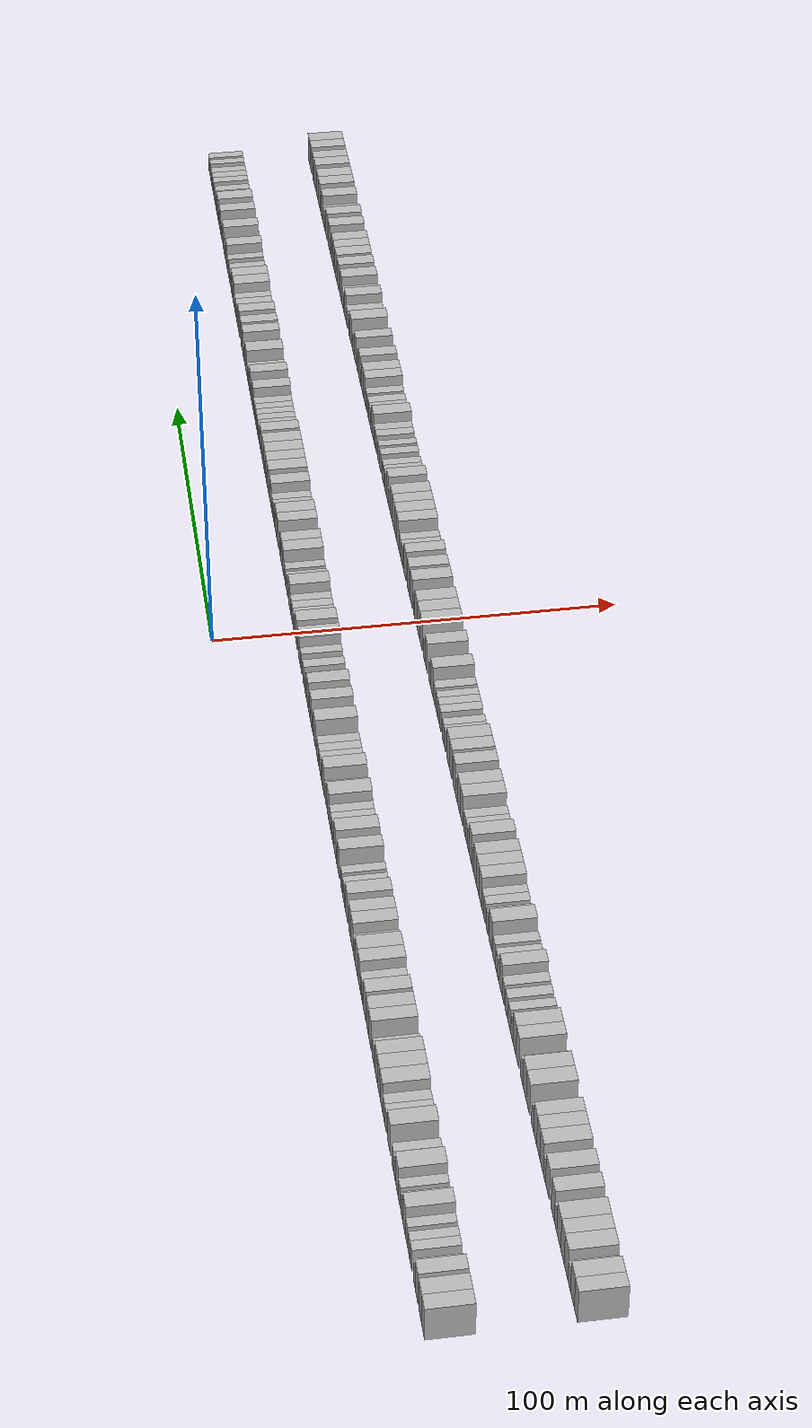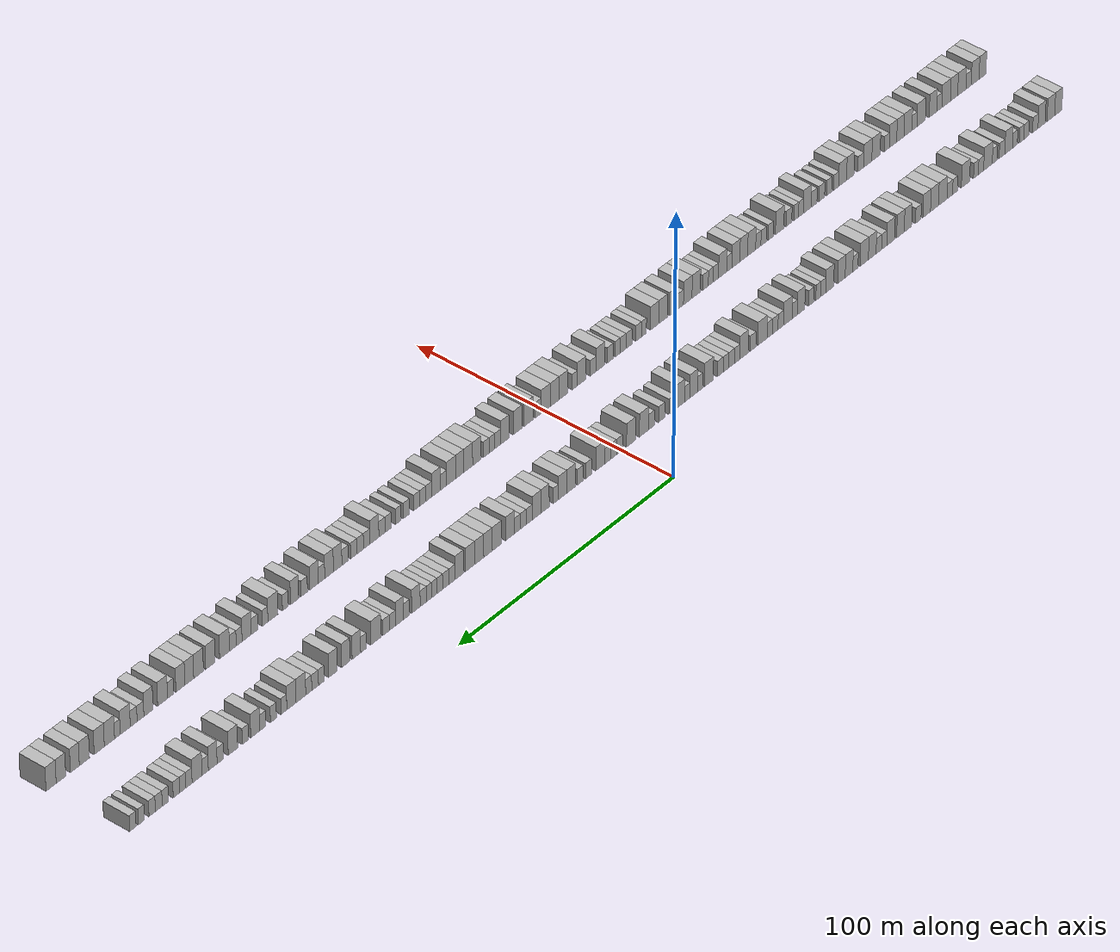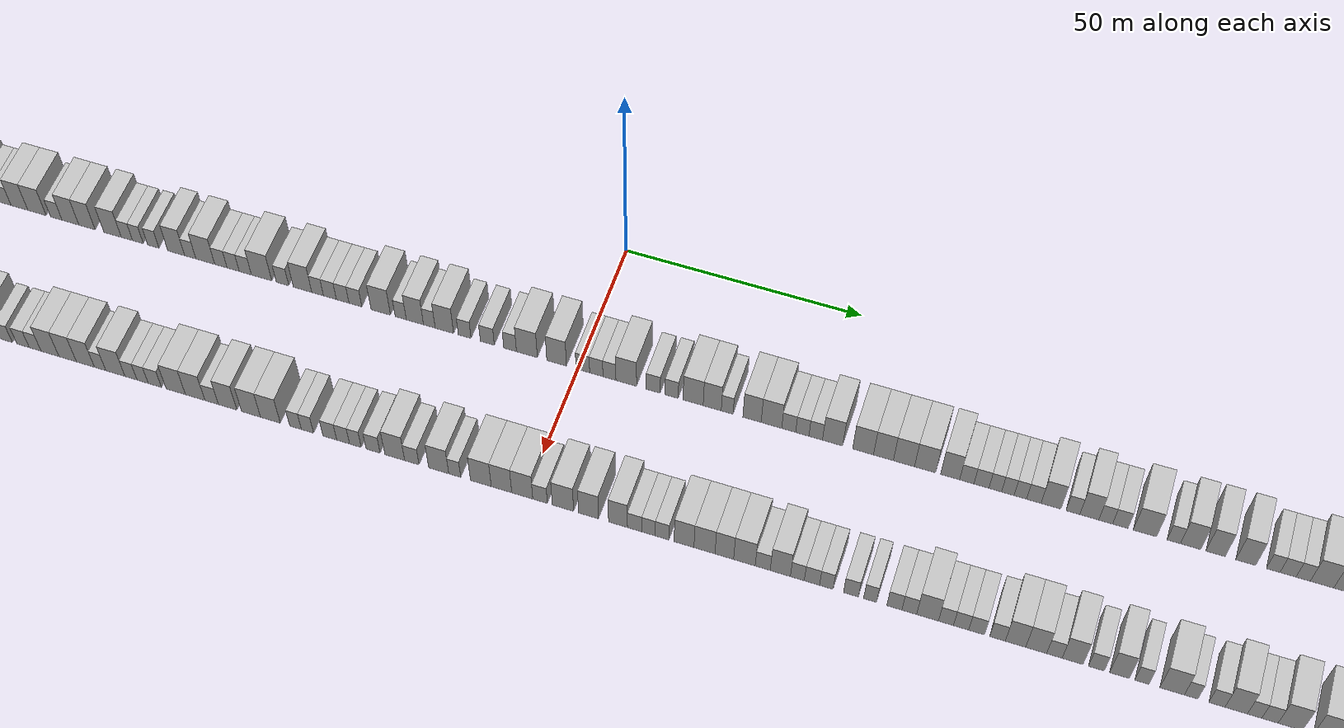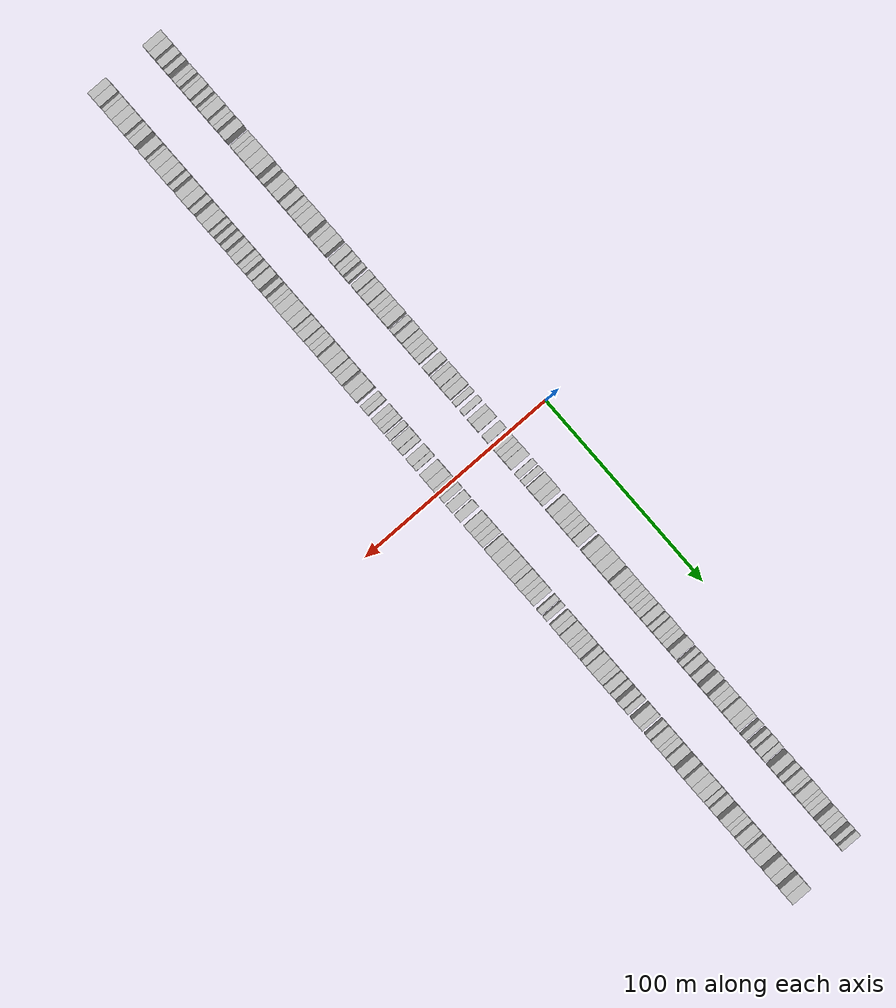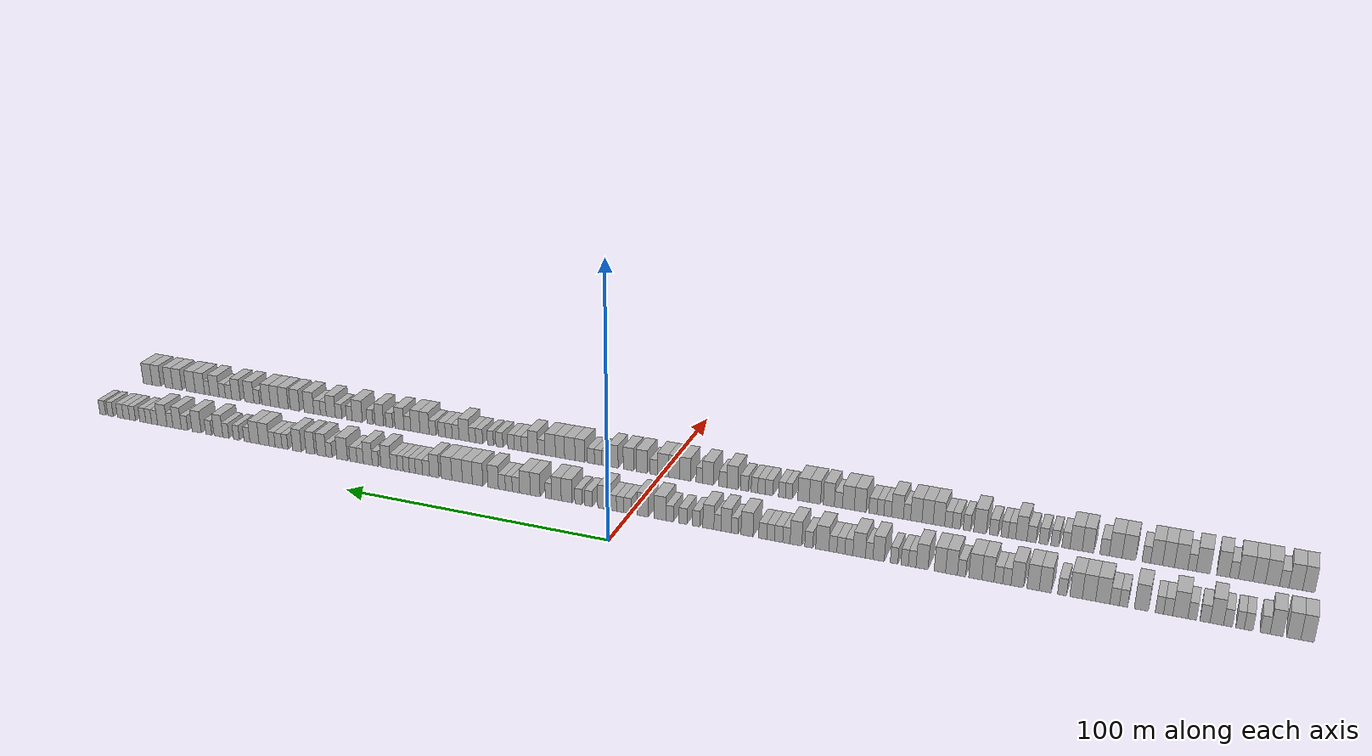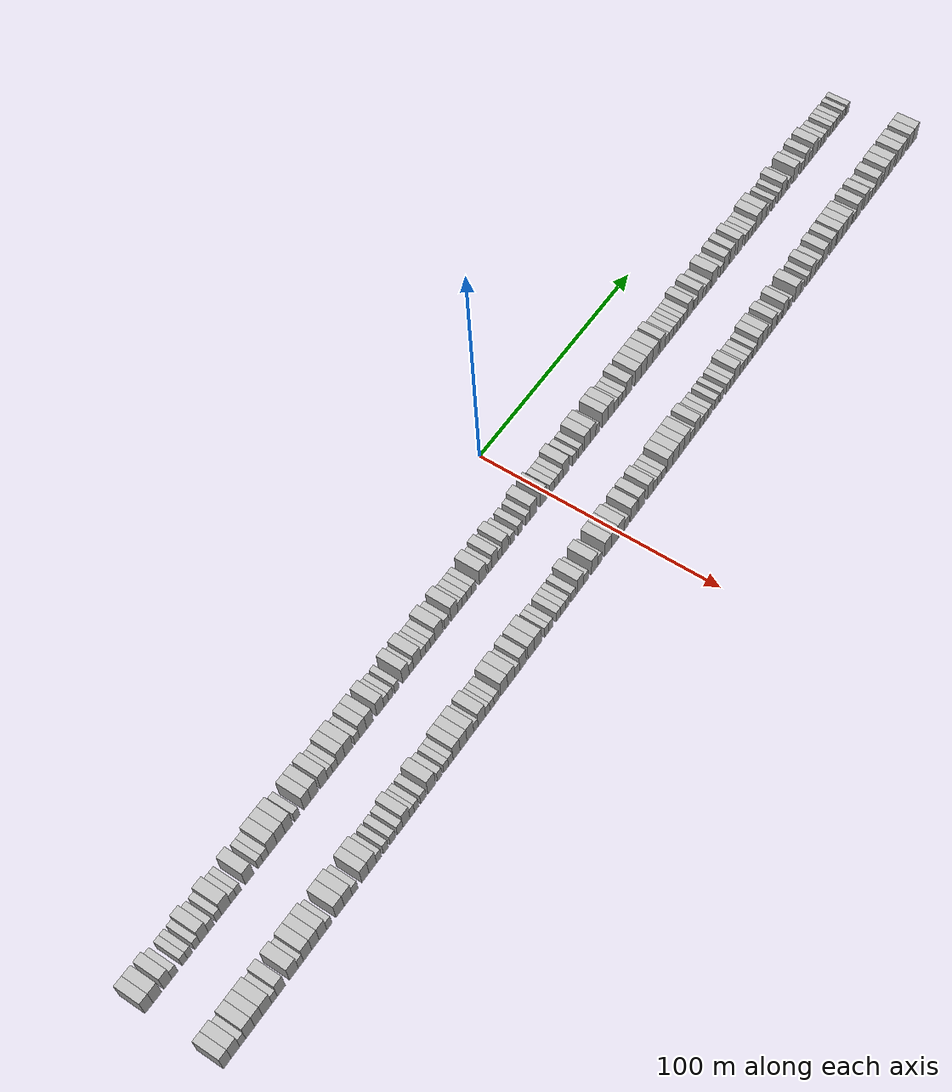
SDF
<sdf version="1.6">
 <world name="default">
  <scene>
   <sky><clouds><speed>12</speed></clouds></sky>
   <ambient>0.4 0.4 0.4 1</ambient>
   <background>0.7 0.7 0.7 1</background>
   <shadows>1</shadows>
  </scene>
  <gravity>0 0 -9.8066</gravity>
  <magnetic_field>6e-06 2.3e-05 -4.2e-05</magnetic_field>
  <physics default="0" name="default_physics" type="ode">
   <ode>
    <solver>
     <type>quick</type>
     <iters>10</iters>
     <sor>1.0</sor>
     <use_dynamic_moi_rescaling>0</use_dynamic_moi_rescaling>
    </solver>
    <constraints>
     <cfm>0</cfm>
     <erp>0.2</erp>
     <contact_max_correcting_vel>100</contact_max_correcting_vel>
     <contact_surface_layer>0.001</contact_surface_layer>
    </constraints>
   </ode>
   <max_step_size>0.004</max_step_size>
   <real_time_factor>1</real_time_factor>
   <real_time_update_rate>250</real_time_update_rate>
  </physics>
  <light name="sun" type="directional">
   <pose>0 0 10 0 0 0</pose>
   <diffuse>0.8 0.8 0.8 1</diffuse>
   <specular>0.2 0.2 0.2 1</specular>
   <attenuation>
    <range>1000</range>
    <constant>0.9</constant>
    <linear>0.01</linear>
    <quadratic>0.001</quadratic>
   </attenuation>
   <direction>-0.5 0.1 -0.9</direction>
  </light>
  <model name="building_1">
   <static>1</static>
   <pose>25.0000 -218.1177 0 0.000000 0.000000 0.000000</pose>
   <link name="link">
    <pose>0 0 4.50 0 0 0</pose>
    <collision name="collision"><geometry><box><size>10.0000 3.7646 9.0000</size></box></geometry></collision>
    <visual name="visual">
     <cast_shadows>0</cast_shadows>
     <geometry><box><size>10.0000 3.7646 9.0000</size></box></geometry>
     <material>
      <script>
       <uri>model://HANNAS_wall/materials/scripts</uri>
       <uri>model://HANNAS_wall/materials/textures</uri>
       <name>vrc/HANNAS_wall</name>
      </script>
     </material>
    </visual>
   </link>
  </model>
  <model name="building_2">
   <static>1</static>
   <pose>25.0000 -214.2348 0 0.000000 0.000000 0.000000</pose>
   <link name="link">
    <pose>0 0 4.50 0 0 0</pose>
    <collision name="collision"><geometry><box><size>10.0000 4.0012 9.0000</size></box></geometry></collision>
    <visual name="visual">
     <cast_shadows>0</cast_shadows>
     <geometry><box><size>10.0000 4.0012 9.0000</size></box></geometry>
     <material>
      <script>
       <uri>model://HANNAS_wall/materials/scripts</uri>
       <uri>model://HANNAS_wall/materials/textures</uri>
       <name>vrc/HANNAS_wall</name>
      </script>
     </material>
    </visual>
   </link>
  </model>
  <model name="building_3">
   <static>1</static>
   <pose>25.0000 -209.3623 0 0.000000 0.000000 0.000000</pose>
   <link name="link">
    <pose>0 0 4.50 0 0 0</pose>
    <collision name="collision"><geometry><box><size>10.0000 3.7438 9.0000</size></box></geometry></collision>
    <visual name="visual">
     <cast_shadows>0</cast_shadows>
     <geometry><box><size>10.0000 3.7438 9.0000</size></box></geometry>
     <material>
      <script>
       <uri>model://HANNAS_wall/materials/scripts</uri>
       <uri>model://HANNAS_wall/materials/textures</uri>
       <name>vrc/HANNAS_wall</name>
      </script>
     </material>
    </visual>
   </link>
  </model>
  <model name="building_4">
   <static>1</static>
   <pose>25.0000 -206.0749 0 0.000000 0.000000 0.000000</pose>
   <link name="link">
    <pose>0 0 3.00 0 0 0</pose>
    <collision name="collision"><geometry><box><size>10.0000 2.8311 6.0000</size></box></geometry></collision>
    <visual name="visual">
     <cast_shadows>0</cast_shadows>
     <geometry><box><size>10.0000 2.8311 6.0000</size></box></geometry>
     <material>
      <script>
       <uri>model://HANNAS_wall/materials/scripts</uri>
       <uri>model://HANNAS_wall/materials/textures</uri>
       <name>vrc/HANNAS_wall</name>
      </script>
     </material>
    </visual>
   </link>
  </model>
  <model name="building_5">
   <static>1</static>
   <pose>25.0000 -201.3900 0 0.000000 0.000000 0.000000</pose>
   <link name="link">
    <pose>0 0 3.00 0 0 0</pose>
    <collision name="collision"><geometry><box><size>10.0000 2.5387 6.0000</size></box></geometry></collision>
    <visual name="visual">
     <cast_shadows>0</cast_shadows>
     <geometry><box><size>10.0000 2.5387 6.0000</size></box></geometry>
     <material>
      <script>
       <uri>model://HANNAS_wall/materials/scripts</uri>
       <uri>model://HANNAS_wall/materials/textures</uri>
       <name>vrc/HANNAS_wall</name>
      </script>
     </material>
    </visual>
   </link>
  </model>
  <model name="building_6">
   <static>1</static>
   <pose>25.0000 -198.9170 0 0.000000 0.000000 0.000000</pose>
   <link name="link">
    <pose>0 0 3.00 0 0 0</pose>
    <collision name="collision"><geometry><box><size>10.0000 2.4074 6.0000</size></box></geometry></collision>
    <visual name="visual">
     <cast_shadows>0</cast_shadows>
     <geometry><box><size>10.0000 2.4074 6.0000</size></box></geometry>
     <material>
      <script>
       <uri>model://HANNAS_wall/materials/scripts</uri>
       <uri>model://HANNAS_wall/materials/textures</uri>
       <name>vrc/HANNAS_wall</name>
      </script>
     </material>
    </visual>
   </link>
  </model>
  <model name="building_7">
   <static>1</static>
   <pose>25.0000 -195.4330 0 0.000000 0.000000 0.000000</pose>
   <link name="link">
    <pose>0 0 3.00 0 0 0</pose>
    <collision name="collision"><geometry><box><size>10.0000 2.5606 6.0000</size></box></geometry></collision>
    <visual name="visual">
     <cast_shadows>0</cast_shadows>
     <geometry><box><size>10.0000 2.5606 6.0000</size></box></geometry>
     <material>
      <script>
       <uri>model://HANNAS_wall/materials/scripts</uri>
       <uri>model://HANNAS_wall/materials/textures</uri>
       <name>vrc/HANNAS_wall</name>
      </script>
     </material>
    </visual>
   </link>
  </model>
  <model name="building_8">
   <static>1</static>
   <pose>25.0000 -192.1857 0 0.000000 0.000000 0.000000</pose>
   <link name="link">
    <pose>0 0 4.50 0 0 0</pose>
    <collision name="collision"><geometry><box><size>10.0000 3.9340 9.0000</size></box></geometry></collision>
    <visual name="visual">
     <cast_shadows>0</cast_shadows>
     <geometry><box><size>10.0000 3.9340 9.0000</size></box></geometry>
     <material>
      <script>
       <uri>model://HANNAS_wall/materials/scripts</uri>
       <uri>model://HANNAS_wall/materials/textures</uri>
       <name>vrc/HANNAS_wall</name>
      </script>
     </material>
    </visual>
   </link>
  </model>
  <model name="building_9">
   <static>1</static>
   <pose>25.0000 -188.7508 0 0.000000 0.000000 0.000000</pose>
   <link name="link">
    <pose>0 0 3.00 0 0 0</pose>
    <collision name="collision"><geometry><box><size>10.0000 2.9357 6.0000</size></box></geometry></collision>
    <visual name="visual">
     <cast_shadows>0</cast_shadows>
     <geometry><box><size>10.0000 2.9357 6.0000</size></box></geometry>
     <material>
      <script>
       <uri>model://HANNAS_wall/materials/scripts</uri>
       <uri>model://HANNAS_wall/materials/textures</uri>
       <name>vrc/HANNAS_wall</name>
      </script>
     </material>
    </visual>
   </link>
  </model>
  <model name="building_10">
   <static>1</static>
   <pose>25.0000 -184.9936 0 0.000000 0.000000 0.000000</pose>
   <link name="link">
    <pose>0 0 3.00 0 0 0</pose>
    <collision name="collision"><geometry><box><size>10.0000 2.5789 6.0000</size></box></geometry></collision>
    <visual name="visual">
     <cast_shadows>0</cast_shadows>
     <geometry><box><size>10.0000 2.5789 6.0000</size></box></geometry>
     <material>
      <script>
       <uri>model://HANNAS_wall/materials/scripts</uri>
       <uri>model://HANNAS_wall/materials/textures</uri>
       <name>vrc/HANNAS_wall</name>
      </script>
     </material>
    </visual>
   </link>
  </model>
  <model name="building_11">
   <static>1</static>
   <pose>25.0000 -181.4808 0 0.000000 0.000000 0.000000</pose>
   <link name="link">
    <pose>0 0 4.50 0 0 0</pose>
    <collision name="collision"><geometry><box><size>10.0000 4.4466 9.0000</size></box></geometry></collision>
    <visual name="visual">
     <cast_shadows>0</cast_shadows>
     <geometry><box><size>10.0000 4.4466 9.0000</size></box></geometry>
     <material>
      <script>
       <uri>model://HANNAS_wall/materials/scripts</uri>
       <uri>model://HANNAS_wall/materials/textures</uri>
       <name>vrc/HANNAS_wall</name>
      </script>
     </material>
    </visual>
   </link>
  </model>
  <model name="building_12">
   <static>1</static>
   <pose>25.0000 -177.8910 0 0.000000 0.000000 0.000000</pose>
   <link name="link">
    <pose>0 0 3.00 0 0 0</pose>
    <collision name="collision"><geometry><box><size>10.0000 2.7331 6.0000</size></box></geometry></collision>
    <visual name="visual">
     <cast_shadows>0</cast_shadows>
     <geometry><box><size>10.0000 2.7331 6.0000</size></box></geometry>
     <material>
      <script>
       <uri>model://HANNAS_wall/materials/scripts</uri>
       <uri>model://HANNAS_wall/materials/textures</uri>
       <name>vrc/HANNAS_wall</name>
      </script>
     </material>
    </visual>
   </link>
  </model>
  <model name="building_13">
   <static>1</static>
   <pose>25.0000 -175.2878 0 0.000000 0.000000 0.000000</pose>
   <link name="link">
    <pose>0 0 3.00 0 0 0</pose>
    <collision name="collision"><geometry><box><size>10.0000 2.4733 6.0000</size></box></geometry></collision>
    <visual name="visual">
     <cast_shadows>0</cast_shadows>
     <geometry><box><size>10.0000 2.4733 6.0000</size></box></geometry>
     <material>
      <script>
       <uri>model://HANNAS_wall/materials/scripts</uri>
       <uri>model://HANNAS_wall/materials/textures</uri>
       <name>vrc/HANNAS_wall</name>
      </script>
     </material>
    </visual>
   </link>
  </model>
  <model name="building_14">
   <static>1</static>
   <pose>25.0000 -169.9233 0 0.000000 0.000000 0.000000</pose>
   <link name="link">
    <pose>0 0 4.50 0 0 0</pose>
    <collision name="collision"><geometry><box><size>10.0000 4.2557 9.0000</size></box></geometry></collision>
    <visual name="visual">
     <cast_shadows>0</cast_shadows>
     <geometry><box><size>10.0000 4.2557 9.0000</size></box></geometry>
     <material>
      <script>
       <uri>model://HANNAS_wall/materials/scripts</uri>
       <uri>model://HANNAS_wall/materials/textures</uri>
       <name>vrc/HANNAS_wall</name>
      </script>
     </material>
    </visual>
   </link>
  </model>
  <model name="building_15">
   <static>1</static>
   <pose>25.0000 -164.5388 0 0.000000 0.000000 0.000000</pose>
   <link name="link">
    <pose>0 0 3.00 0 0 0</pose>
    <collision name="collision"><geometry><box><size>10.0000 2.5134 6.0000</size></box></geometry></collision>
    <visual name="visual">
     <cast_shadows>0</cast_shadows>
     <geometry><box><size>10.0000 2.5134 6.0000</size></box></geometry>
     <material>
      <script>
       <uri>model://HANNAS_wall/materials/scripts</uri>
       <uri>model://HANNAS_wall/materials/textures</uri>
       <name>vrc/HANNAS_wall</name>
      </script>
     </material>
    </visual>
   </link>
  </model>
  <model name="building_16">
   <static>1</static>
   <pose>25.0000 -161.8554 0 0.000000 0.000000 0.000000</pose>
   <link name="link">
    <pose>0 0 3.00 0 0 0</pose>
    <collision name="collision"><geometry><box><size>10.0000 2.8534 6.0000</size></box></geometry></collision>
    <visual name="visual">
     <cast_shadows>0</cast_shadows>
     <geometry><box><size>10.0000 2.8534 6.0000</size></box></geometry>
     <material>
      <script>
       <uri>model://HANNAS_wall/materials/scripts</uri>
       <uri>model://HANNAS_wall/materials/textures</uri>
       <name>vrc/HANNAS_wall</name>
      </script>
     </material>
    </visual>
   </link>
  </model>
  <model name="building_17">
   <static>1</static>
   <pose>25.0000 -158.2648 0 0.000000 0.000000 0.000000</pose>
   <link name="link">
    <pose>0 0 4.50 0 0 0</pose>
    <collision name="collision"><geometry><box><size>10.0000 4.3278 9.0000</size></box></geometry></collision>
    <visual name="visual">
     <cast_shadows>0</cast_shadows>
     <geometry><box><size>10.0000 4.3278 9.0000</size></box></geometry>
     <material>
      <script>
       <uri>model://HANNAS_wall/materials/scripts</uri>
       <uri>model://HANNAS_wall/materials/textures</uri>
       <name>vrc/HANNAS_wall</name>
      </script>
     </material>
    </visual>
   </link>
  </model>
  <model name="building_18">
   <static>1</static>
   <pose>25.0000 -154.0507 0 0.000000 0.000000 0.000000</pose>
   <link name="link">
    <pose>0 0 4.50 0 0 0</pose>
    <collision name="collision"><geometry><box><size>10.0000 4.1003 9.0000</size></box></geometry></collision>
    <visual name="visual">
     <cast_shadows>0</cast_shadows>
     <geometry><box><size>10.0000 4.1003 9.0000</size></box></geometry>
     <material>
      <script>
       <uri>model://HANNAS_wall/materials/scripts</uri>
       <uri>model://HANNAS_wall/materials/textures</uri>
       <name>vrc/HANNAS_wall</name>
      </script>
     </material>
    </visual>
   </link>
  </model>
  <model name="building_19">
   <static>1</static>
   <pose>25.0000 -150.0863 0 0.000000 0.000000 0.000000</pose>
   <link name="link">
    <pose>0 0 4.50 0 0 0</pose>
    <collision name="collision"><geometry><box><size>10.0000 3.8285 9.0000</size></box></geometry></collision>
    <visual name="visual">
     <cast_shadows>0</cast_shadows>
     <geometry><box><size>10.0000 3.8285 9.0000</size></box></geometry>
     <material>
      <script>
       <uri>model://HANNAS_wall/materials/scripts</uri>
       <uri>model://HANNAS_wall/materials/textures</uri>
       <name>vrc/HANNAS_wall</name>
      </script>
     </material>
    </visual>
   </link>
  </model>
  <model name="building_20">
   <static>1</static>
   <pose>25.0000 -145.7861 0 0.000000 0.000000 0.000000</pose>
   <link name="link">
    <pose>0 0 3.00 0 0 0</pose>
    <collision name="collision"><geometry><box><size>10.0000 2.7718 6.0000</size></box></geometry></collision>
    <visual name="visual">
     <cast_shadows>0</cast_shadows>
     <geometry><box><size>10.0000 2.7718 6.0000</size></box></geometry>
     <material>
      <script>
       <uri>model://HANNAS_wall/materials/scripts</uri>
       <uri>model://HANNAS_wall/materials/textures</uri>
       <name>vrc/HANNAS_wall</name>
      </script>
     </material>
    </visual>
   </link>
  </model>
  <model name="building_21">
   <static>1</static>
   <pose>25.0000 -140.5354 0 0.000000 0.000000 0.000000</pose>
   <link name="link">
    <pose>0 0 4.50 0 0 0</pose>
    <collision name="collision"><geometry><box><size>10.0000 3.7296 9.0000</size></box></geometry></collision>
    <visual name="visual">
     <cast_shadows>0</cast_shadows>
     <geometry><box><size>10.0000 3.7296 9.0000</size></box></geometry>
     <material>
      <script>
       <uri>model://HANNAS_wall/materials/scripts</uri>
       <uri>model://HANNAS_wall/materials/textures</uri>
       <name>vrc/HANNAS_wall</name>
      </script>
     </material>
    </visual>
   </link>
  </model>
  <model name="building_22">
   <static>1</static>
   <pose>25.0000 -136.7452 0 0.000000 0.000000 0.000000</pose>
   <link name="link">
    <pose>0 0 4.50 0 0 0</pose>
    <collision name="collision"><geometry><box><size>10.0000 3.8507 9.0000</size></box></geometry></collision>
    <visual name="visual">
     <cast_shadows>0</cast_shadows>
     <geometry><box><size>10.0000 3.8507 9.0000</size></box></geometry>
     <material>
      <script>
       <uri>model://HANNAS_wall/materials/scripts</uri>
       <uri>model://HANNAS_wall/materials/textures</uri>
       <name>vrc/HANNAS_wall</name>
      </script>
     </material>
    </visual>
   </link>
  </model>
  <model name="building_23">
   <static>1</static>
   <pose>25.0000 -131.8363 0 0.000000 0.000000 0.000000</pose>
   <link name="link">
    <pose>0 0 4.50 0 0 0</pose>
    <collision name="collision"><geometry><box><size>10.0000 3.9670 9.0000</size></box></geometry></collision>
    <visual name="visual">
     <cast_shadows>0</cast_shadows>
     <geometry><box><size>10.0000 3.9670 9.0000</size></box></geometry>
     <material>
      <script>
       <uri>model://HANNAS_wall/materials/scripts</uri>
       <uri>model://HANNAS_wall/materials/textures</uri>
       <name>vrc/HANNAS_wall</name>
      </script>
     </material>
    </visual>
   </link>
  </model>
  <model name="building_24">
   <static>1</static>
   <pose>25.0000 -128.5348 0 0.000000 0.000000 0.000000</pose>
   <link name="link">
    <pose>0 0 3.00 0 0 0</pose>
    <collision name="collision"><geometry><box><size>10.0000 2.6360 6.0000</size></box></geometry></collision>
    <visual name="visual">
     <cast_shadows>0</cast_shadows>
     <geometry><box><size>10.0000 2.6360 6.0000</size></box></geometry>
     <material>
      <script>
       <uri>model://HANNAS_wall/materials/scripts</uri>
       <uri>model://HANNAS_wall/materials/textures</uri>
       <name>vrc/HANNAS_wall</name>
      </script>
     </material>
    </visual>
   </link>
  </model>
  <model name="building_25">
   <static>1</static>
   <pose>25.0000 -125.8305 0 0.000000 0.000000 0.000000</pose>
   <link name="link">
    <pose>0 0 3.00 0 0 0</pose>
    <collision name="collision"><geometry><box><size>10.0000 2.7727 6.0000</size></box></geometry></collision>
    <visual name="visual">
     <cast_shadows>0</cast_shadows>
     <geometry><box><size>10.0000 2.7727 6.0000</size></box></geometry>
     <material>
      <script>
       <uri>model://HANNAS_wall/materials/scripts</uri>
       <uri>model://HANNAS_wall/materials/textures</uri>
       <name>vrc/HANNAS_wall</name>
      </script>
     </material>
    </visual>
   </link>
  </model>
  <model name="building_26">
   <static>1</static>
   <pose>25.0000 -122.5052 0 0.000000 0.000000 0.000000</pose>
   <link name="link">
    <pose>0 0 4.50 0 0 0</pose>
    <collision name="collision"><geometry><box><size>10.0000 3.8780 9.0000</size></box></geometry></collision>
    <visual name="visual">
     <cast_shadows>0</cast_shadows>
     <geometry><box><size>10.0000 3.8780 9.0000</size></box></geometry>
     <material>
      <script>
       <uri>model://HANNAS_wall/materials/scripts</uri>
       <uri>model://HANNAS_wall/materials/textures</uri>
       <name>vrc/HANNAS_wall</name>
      </script>
     </material>
    </visual>
   </link>
  </model>
  <model name="building_27">
   <static>1</static>
   <pose>25.0000 -118.4681 0 0.000000 0.000000 0.000000</pose>
   <link name="link">
    <pose>0 0 4.50 0 0 0</pose>
    <collision name="collision"><geometry><box><size>10.0000 4.1962 9.0000</size></box></geometry></collision>
    <visual name="visual">
     <cast_shadows>0</cast_shadows>
     <geometry><box><size>10.0000 4.1962 9.0000</size></box></geometry>
     <material>
      <script>
       <uri>model://HANNAS_wall/materials/scripts</uri>
       <uri>model://HANNAS_wall/materials/textures</uri>
       <name>vrc/HANNAS_wall</name>
      </script>
     </material>
    </visual>
   </link>
  </model>
  <model name="building_28">
   <static>1</static>
   <pose>25.0000 -114.0590 0 0.000000 0.000000 0.000000</pose>
   <link name="link">
    <pose>0 0 3.00 0 0 0</pose>
    <collision name="collision"><geometry><box><size>10.0000 2.6220 6.0000</size></box></geometry></collision>
    <visual name="visual">
     <cast_shadows>0</cast_shadows>
     <geometry><box><size>10.0000 2.6220 6.0000</size></box></geometry>
     <material>
      <script>
       <uri>model://HANNAS_wall/materials/scripts</uri>
       <uri>model://HANNAS_wall/materials/textures</uri>
       <name>vrc/HANNAS_wall</name>
      </script>
     </material>
    </visual>
   </link>
  </model>
  <model name="building_29">
   <static>1</static>
   <pose>25.0000 -110.8329 0 0.000000 0.000000 0.000000</pose>
   <link name="link">
    <pose>0 0 4.50 0 0 0</pose>
    <collision name="collision"><geometry><box><size>10.0000 3.8302 9.0000</size></box></geometry></collision>
    <visual name="visual">
     <cast_shadows>0</cast_shadows>
     <geometry><box><size>10.0000 3.8302 9.0000</size></box></geometry>
     <material>
      <script>
       <uri>model://HANNAS_wall/materials/scripts</uri>
       <uri>model://HANNAS_wall/materials/textures</uri>
       <name>vrc/HANNAS_wall</name>
      </script>
     </material>
    </visual>
   </link>
  </model>
  <model name="building_30">
   <static>1</static>
   <pose>25.0000 -107.0710 0 0.000000 0.000000 0.000000</pose>
   <link name="link">
    <pose>0 0 4.50 0 0 0</pose>
    <collision name="collision"><geometry><box><size>10.0000 3.6937 9.0000</size></box></geometry></collision>
    <visual name="visual">
     <cast_shadows>0</cast_shadows>
     <geometry><box><size>10.0000 3.6937 9.0000</size></box></geometry>
     <material>
      <script>
       <uri>model://HANNAS_wall/materials/scripts</uri>
       <uri>model://HANNAS_wall/materials/textures</uri>
       <name>vrc/HANNAS_wall</name>
      </script>
     </material>
    </visual>
   </link>
  </model>
  <model name="building_31">
   <static>1</static>
   <pose>25.0000 -101.2576 0 0.000000 0.000000 0.000000</pose>
   <link name="link">
    <pose>0 0 4.50 0 0 0</pose>
    <collision name="collision"><geometry><box><size>10.0000 3.9331 9.0000</size></box></geometry></collision>
    <visual name="visual">
     <cast_shadows>0</cast_shadows>
     <geometry><box><size>10.0000 3.9331 9.0000</size></box></geometry>
     <material>
      <script>
       <uri>model://HANNAS_wall/materials/scripts</uri>
       <uri>model://HANNAS_wall/materials/textures</uri>
       <name>vrc/HANNAS_wall</name>
      </script>
     </material>
    </visual>
   </link>
  </model>
  <model name="building_32">
   <static>1</static>
   <pose>25.0000 -98.0210 0 0.000000 0.000000 0.000000</pose>
   <link name="link">
    <pose>0 0 3.00 0 0 0</pose>
    <collision name="collision"><geometry><box><size>10.0000 2.5402 6.0000</size></box></geometry></collision>
    <visual name="visual">
     <cast_shadows>0</cast_shadows>
     <geometry><box><size>10.0000 2.5402 6.0000</size></box></geometry>
     <material>
      <script>
       <uri>model://HANNAS_wall/materials/scripts</uri>
       <uri>model://HANNAS_wall/materials/textures</uri>
       <name>vrc/HANNAS_wall</name>
      </script>
     </material>
    </visual>
   </link>
  </model>
  <model name="building_33">
   <static>1</static>
   <pose>25.0000 -95.5394 0 0.000000 0.000000 0.000000</pose>
   <link name="link">
    <pose>0 0 3.00 0 0 0</pose>
    <collision name="collision"><geometry><box><size>10.0000 2.4229 6.0000</size></box></geometry></collision>
    <visual name="visual">
     <cast_shadows>0</cast_shadows>
     <geometry><box><size>10.0000 2.4229 6.0000</size></box></geometry>
     <material>
      <script>
       <uri>model://HANNAS_wall/materials/scripts</uri>
       <uri>model://HANNAS_wall/materials/textures</uri>
       <name>vrc/HANNAS_wall</name>
      </script>
     </material>
    </visual>
   </link>
  </model>
  <model name="building_34">
   <static>1</static>
   <pose>25.0000 -92.0725 0 0.000000 0.000000 0.000000</pose>
   <link name="link">
    <pose>0 0 3.00 0 0 0</pose>
    <collision name="collision"><geometry><box><size>10.0000 2.5108 6.0000</size></box></geometry></collision>
    <visual name="visual">
     <cast_shadows>0</cast_shadows>
     <geometry><box><size>10.0000 2.5108 6.0000</size></box></geometry>
     <material>
      <script>
       <uri>model://HANNAS_wall/materials/scripts</uri>
       <uri>model://HANNAS_wall/materials/textures</uri>
       <name>vrc/HANNAS_wall</name>
      </script>
     </material>
    </visual>
   </link>
  </model>
  <model name="building_35">
   <static>1</static>
   <pose>25.0000 -86.9352 0 0.000000 0.000000 0.000000</pose>
   <link name="link">
    <pose>0 0 4.50 0 0 0</pose>
    <collision name="collision"><geometry><box><size>10.0000 3.7638 9.0000</size></box></geometry></collision>
    <visual name="visual">
     <cast_shadows>0</cast_shadows>
     <geometry><box><size>10.0000 3.7638 9.0000</size></box></geometry>
     <material>
      <script>
       <uri>model://HANNAS_wall/materials/scripts</uri>
       <uri>model://HANNAS_wall/materials/textures</uri>
       <name>vrc/HANNAS_wall</name>
      </script>
     </material>
    </visual>
   </link>
  </model>
  <model name="building_36">
   <static>1</static>
   <pose>25.0000 -83.7981 0 0.000000 0.000000 0.000000</pose>
   <link name="link">
    <pose>0 0 3.00 0 0 0</pose>
    <collision name="collision"><geometry><box><size>10.0000 2.5105 6.0000</size></box></geometry></collision>
    <visual name="visual">
     <cast_shadows>0</cast_shadows>
     <geometry><box><size>10.0000 2.5105 6.0000</size></box></geometry>
     <material>
      <script>
       <uri>model://HANNAS_wall/materials/scripts</uri>
       <uri>model://HANNAS_wall/materials/textures</uri>
       <name>vrc/HANNAS_wall</name>
      </script>
     </material>
    </visual>
   </link>
  </model>
  <model name="building_37">
   <static>1</static>
   <pose>25.0000 -80.4423 0 0.000000 0.000000 0.000000</pose>
   <link name="link">
    <pose>0 0 4.50 0 0 0</pose>
    <collision name="collision"><geometry><box><size>10.0000 4.2010 9.0000</size></box></geometry></collision>
    <visual name="visual">
     <cast_shadows>0</cast_shadows>
     <geometry><box><size>10.0000 4.2010 9.0000</size></box></geometry>
     <material>
      <script>
       <uri>model://HANNAS_wall/materials/scripts</uri>
       <uri>model://HANNAS_wall/materials/textures</uri>
       <name>vrc/HANNAS_wall</name>
      </script>
     </material>
    </visual>
   </link>
  </model>
  <model name="building_38">
   <static>1</static>
   <pose>25.0000 -76.9729 0 0.000000 0.000000 0.000000</pose>
   <link name="link">
    <pose>0 0 3.00 0 0 0</pose>
    <collision name="collision"><geometry><box><size>10.0000 2.7378 6.0000</size></box></geometry></collision>
    <visual name="visual">
     <cast_shadows>0</cast_shadows>
     <geometry><box><size>10.0000 2.7378 6.0000</size></box></geometry>
     <material>
      <script>
       <uri>model://HANNAS_wall/materials/scripts</uri>
       <uri>model://HANNAS_wall/materials/textures</uri>
       <name>vrc/HANNAS_wall</name>
      </script>
     </material>
    </visual>
   </link>
  </model>
  <model name="building_39">
   <static>1</static>
   <pose>25.0000 -74.2615 0 0.000000 0.000000 0.000000</pose>
   <link name="link">
    <pose>0 0 3.00 0 0 0</pose>
    <collision name="collision"><geometry><box><size>10.0000 2.6850 6.0000</size></box></geometry></collision>
    <visual name="visual">
     <cast_shadows>0</cast_shadows>
     <geometry><box><size>10.0000 2.6850 6.0000</size></box></geometry>
     <material>
      <script>
       <uri>model://HANNAS_wall/materials/scripts</uri>
       <uri>model://HANNAS_wall/materials/textures</uri>
       <name>vrc/HANNAS_wall</name>
      </script>
     </material>
    </visual>
   </link>
  </model>
  <model name="building_40">
   <static>1</static>
   <pose>25.0000 -71.5659 0 0.000000 0.000000 0.000000</pose>
   <link name="link">
    <pose>0 0 3.00 0 0 0</pose>
    <collision name="collision"><geometry><box><size>10.0000 2.7063 6.0000</size></box></geometry></collision>
    <visual name="visual">
     <cast_shadows>0</cast_shadows>
     <geometry><box><size>10.0000 2.7063 6.0000</size></box></geometry>
     <material>
      <script>
       <uri>model://HANNAS_wall/materials/scripts</uri>
       <uri>model://HANNAS_wall/materials/textures</uri>
       <name>vrc/HANNAS_wall</name>
      </script>
     </material>
    </visual>
   </link>
  </model>
  <model name="building_41">
   <static>1</static>
   <pose>25.0000 -67.9681 0 0.000000 0.000000 0.000000</pose>
   <link name="link">
    <pose>0 0 4.50 0 0 0</pose>
    <collision name="collision"><geometry><box><size>10.0000 4.4892 9.0000</size></box></geometry></collision>
    <visual name="visual">
     <cast_shadows>0</cast_shadows>
     <geometry><box><size>10.0000 4.4892 9.0000</size></box></geometry>
     <material>
      <script>
       <uri>model://HANNAS_wall/materials/scripts</uri>
       <uri>model://HANNAS_wall/materials/textures</uri>
       <name>vrc/HANNAS_wall</name>
      </script>
     </material>
    </visual>
   </link>
  </model>
  <model name="building_42">
   <static>1</static>
   <pose>25.0000 -63.3430 0 0.000000 0.000000 0.000000</pose>
   <link name="link">
    <pose>0 0 3.00 0 0 0</pose>
    <collision name="collision"><geometry><box><size>10.0000 2.7610 6.0000</size></box></geometry></collision>
    <visual name="visual">
     <cast_shadows>0</cast_shadows>
     <geometry><box><size>10.0000 2.7610 6.0000</size></box></geometry>
     <material>
      <script>
       <uri>model://HANNAS_wall/materials/scripts</uri>
       <uri>model://HANNAS_wall/materials/textures</uri>
       <name>vrc/HANNAS_wall</name>
      </script>
     </material>
    </visual>
   </link>
  </model>
  <model name="building_43">
   <static>1</static>
   <pose>25.0000 -58.9447 0 0.000000 0.000000 0.000000</pose>
   <link name="link">
    <pose>0 0 4.50 0 0 0</pose>
    <collision name="collision"><geometry><box><size>10.0000 4.0356 9.0000</size></box></geometry></collision>
    <visual name="visual">
     <cast_shadows>0</cast_shadows>
     <geometry><box><size>10.0000 4.0356 9.0000</size></box></geometry>
     <material>
      <script>
       <uri>model://HANNAS_wall/materials/scripts</uri>
       <uri>model://HANNAS_wall/materials/textures</uri>
       <name>vrc/HANNAS_wall</name>
      </script>
     </material>
    </visual>
   </link>
  </model>
  <model name="building_44">
   <static>1</static>
   <pose>25.0000 -55.6526 0 0.000000 0.000000 0.000000</pose>
   <link name="link">
    <pose>0 0 3.00 0 0 0</pose>
    <collision name="collision"><geometry><box><size>10.0000 2.5485 6.0000</size></box></geometry></collision>
    <visual name="visual">
     <cast_shadows>0</cast_shadows>
     <geometry><box><size>10.0000 2.5485 6.0000</size></box></geometry>
     <material>
      <script>
       <uri>model://HANNAS_wall/materials/scripts</uri>
       <uri>model://HANNAS_wall/materials/textures</uri>
       <name>vrc/HANNAS_wall</name>
      </script>
     </material>
    </visual>
   </link>
  </model>
  <model name="building_45">
   <static>1</static>
   <pose>25.0000 -52.9642 0 0.000000 0.000000 0.000000</pose>
   <link name="link">
    <pose>0 0 3.00 0 0 0</pose>
    <collision name="collision"><geometry><box><size>10.0000 2.8284 6.0000</size></box></geometry></collision>
    <visual name="visual">
     <cast_shadows>0</cast_shadows>
     <geometry><box><size>10.0000 2.8284 6.0000</size></box></geometry>
     <material>
      <script>
       <uri>model://HANNAS_wall/materials/scripts</uri>
       <uri>model://HANNAS_wall/materials/textures</uri>
       <name>vrc/HANNAS_wall</name>
      </script>
     </material>
    </visual>
   </link>
  </model>
  <model name="building_46">
   <static>1</static>
   <pose>25.0000 -50.1796 0 0.000000 0.000000 0.000000</pose>
   <link name="link">
    <pose>0 0 3.00 0 0 0</pose>
    <collision name="collision"><geometry><box><size>10.0000 2.7408 6.0000</size></box></geometry></collision>
    <visual name="visual">
     <cast_shadows>0</cast_shadows>
     <geometry><box><size>10.0000 2.7408 6.0000</size></box></geometry>
     <material>
      <script>
       <uri>model://HANNAS_wall/materials/scripts</uri>
       <uri>model://HANNAS_wall/materials/textures</uri>
       <name>vrc/HANNAS_wall</name>
      </script>
     </material>
    </visual>
   </link>
  </model>
  <model name="building_47">
   <static>1</static>
   <pose>25.0000 -47.4117 0 0.000000 0.000000 0.000000</pose>
   <link name="link">
    <pose>0 0 3.00 0 0 0</pose>
    <collision name="collision"><geometry><box><size>10.0000 2.7948 6.0000</size></box></geometry></collision>
    <visual name="visual">
     <cast_shadows>0</cast_shadows>
     <geometry><box><size>10.0000 2.7948 6.0000</size></box></geometry>
     <material>
      <script>
       <uri>model://HANNAS_wall/materials/scripts</uri>
       <uri>model://HANNAS_wall/materials/textures</uri>
       <name>vrc/HANNAS_wall</name>
      </script>
     </material>
    </visual>
   </link>
  </model>
  <model name="building_48">
   <static>1</static>
   <pose>25.0000 -41.9068 0 0.000000 0.000000 0.000000</pose>
   <link name="link">
    <pose>0 0 4.50 0 0 0</pose>
    <collision name="collision"><geometry><box><size>10.0000 4.2150 9.0000</size></box></geometry></collision>
    <visual name="visual">
     <cast_shadows>0</cast_shadows>
     <geometry><box><size>10.0000 4.2150 9.0000</size></box></geometry>
     <material>
      <script>
       <uri>model://HANNAS_wall/materials/scripts</uri>
       <uri>model://HANNAS_wall/materials/textures</uri>
       <name>vrc/HANNAS_wall</name>
      </script>
     </material>
    </visual>
   </link>
  </model>
  <model name="building_49">
   <static>1</static>
   <pose>25.0000 -37.5975 0 0.000000 0.000000 0.000000</pose>
   <link name="link">
    <pose>0 0 3.00 0 0 0</pose>
    <collision name="collision"><geometry><box><size>10.0000 2.4036 6.0000</size></box></geometry></collision>
    <visual name="visual">
     <cast_shadows>0</cast_shadows>
     <geometry><box><size>10.0000 2.4036 6.0000</size></box></geometry>
     <material>
      <script>
       <uri>model://HANNAS_wall/materials/scripts</uri>
       <uri>model://HANNAS_wall/materials/textures</uri>
       <name>vrc/HANNAS_wall</name>
      </script>
     </material>
    </visual>
   </link>
  </model>
  <model name="building_50">
   <static>1</static>
   <pose>25.0000 -34.5441 0 0.000000 0.000000 0.000000</pose>
   <link name="link">
    <pose>0 0 4.50 0 0 0</pose>
    <collision name="collision"><geometry><box><size>10.0000 3.7032 9.0000</size></box></geometry></collision>
    <visual name="visual">
     <cast_shadows>0</cast_shadows>
     <geometry><box><size>10.0000 3.7032 9.0000</size></box></geometry>
     <material>
      <script>
       <uri>model://HANNAS_wall/materials/scripts</uri>
       <uri>model://HANNAS_wall/materials/textures</uri>
       <name>vrc/HANNAS_wall</name>
      </script>
     </material>
    </visual>
   </link>
  </model>
  <model name="building_51">
   <static>1</static>
   <pose>25.0000 -31.4358 0 0.000000 0.000000 0.000000</pose>
   <link name="link">
    <pose>0 0 3.00 0 0 0</pose>
    <collision name="collision"><geometry><box><size>10.0000 2.5134 6.0000</size></box></geometry></collision>
    <visual name="visual">
     <cast_shadows>0</cast_shadows>
     <geometry><box><size>10.0000 2.5134 6.0000</size></box></geometry>
     <material>
      <script>
       <uri>model://HANNAS_wall/materials/scripts</uri>
       <uri>model://HANNAS_wall/materials/textures</uri>
       <name>vrc/HANNAS_wall</name>
      </script>
     </material>
    </visual>
   </link>
  </model>
  <model name="building_52">
   <static>1</static>
   <pose>25.0000 -28.2039 0 0.000000 0.000000 0.000000</pose>
   <link name="link">
    <pose>0 0 4.50 0 0 0</pose>
    <collision name="collision"><geometry><box><size>10.0000 3.9502 9.0000</size></box></geometry></collision>
    <visual name="visual">
     <cast_shadows>0</cast_shadows>
     <geometry><box><size>10.0000 3.9502 9.0000</size></box></geometry>
     <material>
      <script>
       <uri>model://HANNAS_wall/materials/scripts</uri>
       <uri>model://HANNAS_wall/materials/textures</uri>
       <name>vrc/HANNAS_wall</name>
      </script>
     </material>
    </visual>
   </link>
  </model>
  <model name="building_53">
   <static>1</static>
   <pose>25.0000 -23.8718 0 0.000000 0.000000 0.000000</pose>
   <link name="link">
    <pose>0 0 3.00 0 0 0</pose>
    <collision name="collision"><geometry><box><size>10.0000 2.7140 6.0000</size></box></geometry></collision>
    <visual name="visual">
     <cast_shadows>0</cast_shadows>
     <geometry><box><size>10.0000 2.7140 6.0000</size></box></geometry>
     <material>
      <script>
       <uri>model://HANNAS_wall/materials/scripts</uri>
       <uri>model://HANNAS_wall/materials/textures</uri>
       <name>vrc/HANNAS_wall</name>
      </script>
     </material>
    </visual>
   </link>
  </model>
  <model name="building_54">
   <static>1</static>
   <pose>25.0000 -19.0356 0 0.000000 0.000000 0.000000</pose>
   <link name="link">
    <pose>0 0 3.00 0 0 0</pose>
    <collision name="collision"><geometry><box><size>10.0000 2.9583 6.0000</size></box></geometry></collision>
    <visual name="visual">
     <cast_shadows>0</cast_shadows>
     <geometry><box><size>10.0000 2.9583 6.0000</size></box></geometry>
     <material>
      <script>
       <uri>model://HANNAS_wall/materials/scripts</uri>
       <uri>model://HANNAS_wall/materials/textures</uri>
       <name>vrc/HANNAS_wall</name>
      </script>
     </material>
    </visual>
   </link>
  </model>
  <model name="building_55">
   <static>1</static>
   <pose>25.0000 -14.2076 0 0.000000 0.000000 0.000000</pose>
   <link name="link">
    <pose>0 0 3.00 0 0 0</pose>
    <collision name="collision"><geometry><box><size>10.0000 2.6978 6.0000</size></box></geometry></collision>
    <visual name="visual">
     <cast_shadows>0</cast_shadows>
     <geometry><box><size>10.0000 2.6978 6.0000</size></box></geometry>
     <material>
      <script>
       <uri>model://HANNAS_wall/materials/scripts</uri>
       <uri>model://HANNAS_wall/materials/textures</uri>
       <name>vrc/HANNAS_wall</name>
      </script>
     </material>
    </visual>
   </link>
  </model>
  <model name="building_56">
   <static>1</static>
   <pose>25.0000 -10.6530 0 0.000000 0.000000 0.000000</pose>
   <link name="link">
    <pose>0 0 4.50 0 0 0</pose>
    <collision name="collision"><geometry><box><size>10.0000 4.4113 9.0000</size></box></geometry></collision>
    <visual name="visual">
     <cast_shadows>0</cast_shadows>
     <geometry><box><size>10.0000 4.4113 9.0000</size></box></geometry>
     <material>
      <script>
       <uri>model://HANNAS_wall/materials/scripts</uri>
       <uri>model://HANNAS_wall/materials/textures</uri>
       <name>vrc/HANNAS_wall</name>
      </script>
     </material>
    </visual>
   </link>
  </model>
  <model name="building_57">
   <static>1</static>
   <pose>25.0000 -4.3810 0 0.000000 0.000000 0.000000</pose>
   <link name="link">
    <pose>0 0 4.50 0 0 0</pose>
    <collision name="collision"><geometry><box><size>10.0000 4.1327 9.0000</size></box></geometry></collision>
    <visual name="visual">
     <cast_shadows>0</cast_shadows>
     <geometry><box><size>10.0000 4.1327 9.0000</size></box></geometry>
     <material>
      <script>
       <uri>model://HANNAS_wall/materials/scripts</uri>
       <uri>model://HANNAS_wall/materials/textures</uri>
       <name>vrc/HANNAS_wall</name>
      </script>
     </material>
    </visual>
   </link>
  </model>
  <model name="building_58">
   <static>1</static>
   <pose>25.0000 1.1150 0 0.000000 0.000000 0.000000</pose>
   <link name="link">
    <pose>0 0 3.00 0 0 0</pose>
    <collision name="collision"><geometry><box><size>10.0000 2.8594 6.0000</size></box></geometry></collision>
    <visual name="visual">
     <cast_shadows>0</cast_shadows>
     <geometry><box><size>10.0000 2.8594 6.0000</size></box></geometry>
     <material>
      <script>
       <uri>model://HANNAS_wall/materials/scripts</uri>
       <uri>model://HANNAS_wall/materials/textures</uri>
       <name>vrc/HANNAS_wall</name>
      </script>
     </material>
    </visual>
   </link>
  </model>
  <model name="building_59">
   <static>1</static>
   <pose>25.0000 3.9281 0 0.000000 0.000000 0.000000</pose>
   <link name="link">
    <pose>0 0 3.00 0 0 0</pose>
    <collision name="collision"><geometry><box><size>10.0000 2.7669 6.0000</size></box></geometry></collision>
    <visual name="visual">
     <cast_shadows>0</cast_shadows>
     <geometry><box><size>10.0000 2.7669 6.0000</size></box></geometry>
     <material>
      <script>
       <uri>model://HANNAS_wall/materials/scripts</uri>
       <uri>model://HANNAS_wall/materials/textures</uri>
       <name>vrc/HANNAS_wall</name>
      </script>
     </material>
    </visual>
   </link>
  </model>
  <model name="building_60">
   <static>1</static>
   <pose>25.0000 6.6697 0 0.000000 0.000000 0.000000</pose>
   <link name="link">
    <pose>0 0 3.00 0 0 0</pose>
    <collision name="collision"><geometry><box><size>10.0000 2.7162 6.0000</size></box></geometry></collision>
    <visual name="visual">
     <cast_shadows>0</cast_shadows>
     <geometry><box><size>10.0000 2.7162 6.0000</size></box></geometry>
     <material>
      <script>
       <uri>model://HANNAS_wall/materials/scripts</uri>
       <uri>model://HANNAS_wall/materials/textures</uri>
       <name>vrc/HANNAS_wall</name>
      </script>
     </material>
    </visual>
   </link>
  </model>
  <model name="building_61">
   <static>1</static>
   <pose>25.0000 10.1709 0 0.000000 0.000000 0.000000</pose>
   <link name="link">
    <pose>0 0 4.50 0 0 0</pose>
    <collision name="collision"><geometry><box><size>10.0000 4.2864 9.0000</size></box></geometry></collision>
    <visual name="visual">
     <cast_shadows>0</cast_shadows>
     <geometry><box><size>10.0000 4.2864 9.0000</size></box></geometry>
     <material>
      <script>
       <uri>model://HANNAS_wall/materials/scripts</uri>
       <uri>model://HANNAS_wall/materials/textures</uri>
       <name>vrc/HANNAS_wall</name>
      </script>
     </material>
    </visual>
   </link>
  </model>
  <model name="building_62">
   <static>1</static>
   <pose>25.0000 15.7684 0 0.000000 0.000000 0.000000</pose>
   <link name="link">
    <pose>0 0 3.00 0 0 0</pose>
    <collision name="collision"><geometry><box><size>10.0000 2.9085 6.0000</size></box></geometry></collision>
    <visual name="visual">
     <cast_shadows>0</cast_shadows>
     <geometry><box><size>10.0000 2.9085 6.0000</size></box></geometry>
     <material>
      <script>
       <uri>model://HANNAS_wall/materials/scripts</uri>
       <uri>model://HANNAS_wall/materials/textures</uri>
       <name>vrc/HANNAS_wall</name>
      </script>
     </material>
    </visual>
   </link>
  </model>
  <model name="building_63">
   <static>1</static>
   <pose>25.0000 19.5804 0 0.000000 0.000000 0.000000</pose>
   <link name="link">
    <pose>0 0 3.00 0 0 0</pose>
    <collision name="collision"><geometry><box><size>10.0000 2.7154 6.0000</size></box></geometry></collision>
    <visual name="visual">
     <cast_shadows>0</cast_shadows>
     <geometry><box><size>10.0000 2.7154 6.0000</size></box></geometry>
     <material>
      <script>
       <uri>model://HANNAS_wall/materials/scripts</uri>
       <uri>model://HANNAS_wall/materials/textures</uri>
       <name>vrc/HANNAS_wall</name>
      </script>
     </material>
    </visual>
   </link>
  </model>
  <model name="building_64">
   <static>1</static>
   <pose>25.0000 24.0106 0 0.000000 0.000000 0.000000</pose>
   <link name="link">
    <pose>0 0 4.50 0 0 0</pose>
    <collision name="collision"><geometry><box><size>10.0000 4.1451 9.0000</size></box></geometry></collision>
    <visual name="visual">
     <cast_shadows>0</cast_shadows>
     <geometry><box><size>10.0000 4.1451 9.0000</size></box></geometry>
     <material>
      <script>
       <uri>model://HANNAS_wall/materials/scripts</uri>
       <uri>model://HANNAS_wall/materials/textures</uri>
       <name>vrc/HANNAS_wall</name>
      </script>
     </material>
    </visual>
   </link>
  </model>
  <model name="building_65">
   <static>1</static>
   <pose>25.0000 27.9372 0 0.000000 0.000000 0.000000</pose>
   <link name="link">
    <pose>0 0 4.50 0 0 0</pose>
    <collision name="collision"><geometry><box><size>10.0000 3.7080 9.0000</size></box></geometry></collision>
    <visual name="visual">
     <cast_shadows>0</cast_shadows>
     <geometry><box><size>10.0000 3.7080 9.0000</size></box></geometry>
     <material>
      <script>
       <uri>model://HANNAS_wall/materials/scripts</uri>
       <uri>model://HANNAS_wall/materials/textures</uri>
       <name>vrc/HANNAS_wall</name>
      </script>
     </material>
    </visual>
   </link>
  </model>
  <model name="building_66">
   <static>1</static>
   <pose>25.0000 31.0018 0 0.000000 0.000000 0.000000</pose>
   <link name="link">
    <pose>0 0 3.00 0 0 0</pose>
    <collision name="collision"><geometry><box><size>10.0000 2.4212 6.0000</size></box></geometry></collision>
    <visual name="visual">
     <cast_shadows>0</cast_shadows>
     <geometry><box><size>10.0000 2.4212 6.0000</size></box></geometry>
     <material>
      <script>
       <uri>model://HANNAS_wall/materials/scripts</uri>
       <uri>model://HANNAS_wall/materials/textures</uri>
       <name>vrc/HANNAS_wall</name>
      </script>
     </material>
    </visual>
   </link>
  </model>
  <model name="building_67">
   <static>1</static>
   <pose>25.0000 36.0762 0 0.000000 0.000000 0.000000</pose>
   <link name="link">
    <pose>0 0 4.50 0 0 0</pose>
    <collision name="collision"><geometry><box><size>10.0000 3.7278 9.0000</size></box></geometry></collision>
    <visual name="visual">
     <cast_shadows>0</cast_shadows>
     <geometry><box><size>10.0000 3.7278 9.0000</size></box></geometry>
     <material>
      <script>
       <uri>model://HANNAS_wall/materials/scripts</uri>
       <uri>model://HANNAS_wall/materials/textures</uri>
       <name>vrc/HANNAS_wall</name>
      </script>
     </material>
    </visual>
   </link>
  </model>
  <model name="building_68">
   <static>1</static>
   <pose>25.0000 40.0286 0 0.000000 0.000000 0.000000</pose>
   <link name="link">
    <pose>0 0 4.50 0 0 0</pose>
    <collision name="collision"><geometry><box><size>10.0000 4.1769 9.0000</size></box></geometry></collision>
    <visual name="visual">
     <cast_shadows>0</cast_shadows>
     <geometry><box><size>10.0000 4.1769 9.0000</size></box></geometry>
     <material>
      <script>
       <uri>model://HANNAS_wall/materials/scripts</uri>
       <uri>model://HANNAS_wall/materials/textures</uri>
       <name>vrc/HANNAS_wall</name>
      </script>
     </material>
    </visual>
   </link>
  </model>
  <model name="building_69">
   <static>1</static>
   <pose>25.0000 43.5361 0 0.000000 0.000000 0.000000</pose>
   <link name="link">
    <pose>0 0 3.00 0 0 0</pose>
    <collision name="collision"><geometry><box><size>10.0000 2.8380 6.0000</size></box></geometry></collision>
    <visual name="visual">
     <cast_shadows>0</cast_shadows>
     <geometry><box><size>10.0000 2.8380 6.0000</size></box></geometry>
     <material>
      <script>
       <uri>model://HANNAS_wall/materials/scripts</uri>
       <uri>model://HANNAS_wall/materials/textures</uri>
       <name>vrc/HANNAS_wall</name>
      </script>
     </material>
    </visual>
   </link>
  </model>
  <model name="building_70">
   <static>1</static>
   <pose>25.0000 46.2946 0 0.000000 0.000000 0.000000</pose>
   <link name="link">
    <pose>0 0 3.00 0 0 0</pose>
    <collision name="collision"><geometry><box><size>10.0000 2.6791 6.0000</size></box></geometry></collision>
    <visual name="visual">
     <cast_shadows>0</cast_shadows>
     <geometry><box><size>10.0000 2.6791 6.0000</size></box></geometry>
     <material>
      <script>
       <uri>model://HANNAS_wall/materials/scripts</uri>
       <uri>model://HANNAS_wall/materials/textures</uri>
       <name>vrc/HANNAS_wall</name>
      </script>
     </material>
    </visual>
   </link>
  </model>
  <model name="building_71">
   <static>1</static>
   <pose>25.0000 49.0042 0 0.000000 0.000000 0.000000</pose>
   <link name="link">
    <pose>0 0 3.00 0 0 0</pose>
    <collision name="collision"><geometry><box><size>10.0000 2.7400 6.0000</size></box></geometry></collision>
    <visual name="visual">
     <cast_shadows>0</cast_shadows>
     <geometry><box><size>10.0000 2.7400 6.0000</size></box></geometry>
     <material>
      <script>
       <uri>model://HANNAS_wall/materials/scripts</uri>
       <uri>model://HANNAS_wall/materials/textures</uri>
       <name>vrc/HANNAS_wall</name>
      </script>
     </material>
    </visual>
   </link>
  </model>
  <model name="building_72">
   <static>1</static>
   <pose>25.0000 52.4080 0 0.000000 0.000000 0.000000</pose>
   <link name="link">
    <pose>0 0 4.50 0 0 0</pose>
    <collision name="collision"><geometry><box><size>10.0000 4.0677 9.0000</size></box></geometry></collision>
    <visual name="visual">
     <cast_shadows>0</cast_shadows>
     <geometry><box><size>10.0000 4.0677 9.0000</size></box></geometry>
     <material>
      <script>
       <uri>model://HANNAS_wall/materials/scripts</uri>
       <uri>model://HANNAS_wall/materials/textures</uri>
       <name>vrc/HANNAS_wall</name>
      </script>
     </material>
    </visual>
   </link>
  </model>
  <model name="building_73">
   <static>1</static>
   <pose>25.0000 58.5388 0 0.000000 0.000000 0.000000</pose>
   <link name="link">
    <pose>0 0 4.50 0 0 0</pose>
    <collision name="collision"><geometry><box><size>10.0000 4.1938 9.0000</size></box></geometry></collision>
    <visual name="visual">
     <cast_shadows>0</cast_shadows>
     <geometry><box><size>10.0000 4.1938 9.0000</size></box></geometry>
     <material>
      <script>
       <uri>model://HANNAS_wall/materials/scripts</uri>
       <uri>model://HANNAS_wall/materials/textures</uri>
       <name>vrc/HANNAS_wall</name>
      </script>
     </material>
    </visual>
   </link>
  </model>
  <model name="building_74">
   <static>1</static>
   <pose>25.0000 62.6216 0 0.000000 0.000000 0.000000</pose>
   <link name="link">
    <pose>0 0 4.50 0 0 0</pose>
    <collision name="collision"><geometry><box><size>10.0000 3.9719 9.0000</size></box></geometry></collision>
    <visual name="visual">
     <cast_shadows>0</cast_shadows>
     <geometry><box><size>10.0000 3.9719 9.0000</size></box></geometry>
     <material>
      <script>
       <uri>model://HANNAS_wall/materials/scripts</uri>
       <uri>model://HANNAS_wall/materials/textures</uri>
       <name>vrc/HANNAS_wall</name>
      </script>
     </material>
    </visual>
   </link>
  </model>
  <model name="building_75">
   <static>1</static>
   <pose>25.0000 66.7093 0 0.000000 0.000000 0.000000</pose>
   <link name="link">
    <pose>0 0 4.50 0 0 0</pose>
    <collision name="collision"><geometry><box><size>10.0000 4.2034 9.0000</size></box></geometry></collision>
    <visual name="visual">
     <cast_shadows>0</cast_shadows>
     <geometry><box><size>10.0000 4.2034 9.0000</size></box></geometry>
     <material>
      <script>
       <uri>model://HANNAS_wall/materials/scripts</uri>
       <uri>model://HANNAS_wall/materials/textures</uri>
       <name>vrc/HANNAS_wall</name>
      </script>
     </material>
    </visual>
   </link>
  </model>
  <model name="building_76">
   <static>1</static>
   <pose>25.0000 70.8967 0 0.000000 0.000000 0.000000</pose>
   <link name="link">
    <pose>0 0 4.50 0 0 0</pose>
    <collision name="collision"><geometry><box><size>10.0000 4.1715 9.0000</size></box></geometry></collision>
    <visual name="visual">
     <cast_shadows>0</cast_shadows>
     <geometry><box><size>10.0000 4.1715 9.0000</size></box></geometry>
     <material>
      <script>
       <uri>model://HANNAS_wall/materials/scripts</uri>
       <uri>model://HANNAS_wall/materials/textures</uri>
       <name>vrc/HANNAS_wall</name>
      </script>
     </material>
    </visual>
   </link>
  </model>
  <model name="building_77">
   <static>1</static>
   <pose>25.0000 75.8681 0 0.000000 0.000000 0.000000</pose>
   <link name="link">
    <pose>0 0 4.50 0 0 0</pose>
    <collision name="collision"><geometry><box><size>10.0000 3.7712 9.0000</size></box></geometry></collision>
    <visual name="visual">
     <cast_shadows>0</cast_shadows>
     <geometry><box><size>10.0000 3.7712 9.0000</size></box></geometry>
     <material>
      <script>
       <uri>model://HANNAS_wall/materials/scripts</uri>
       <uri>model://HANNAS_wall/materials/textures</uri>
       <name>vrc/HANNAS_wall</name>
      </script>
     </material>
    </visual>
   </link>
  </model>
  <model name="building_78">
   <static>1</static>
   <pose>25.0000 79.1650 0 0.000000 0.000000 0.000000</pose>
   <link name="link">
    <pose>0 0 3.00 0 0 0</pose>
    <collision name="collision"><geometry><box><size>10.0000 2.8226 6.0000</size></box></geometry></collision>
    <visual name="visual">
     <cast_shadows>0</cast_shadows>
     <geometry><box><size>10.0000 2.8226 6.0000</size></box></geometry>
     <material>
      <script>
       <uri>model://HANNAS_wall/materials/scripts</uri>
       <uri>model://HANNAS_wall/materials/textures</uri>
       <name>vrc/HANNAS_wall</name>
      </script>
     </material>
    </visual>
   </link>
  </model>
  <model name="building_79">
   <static>1</static>
   <pose>25.0000 82.0449 0 0.000000 0.000000 0.000000</pose>
   <link name="link">
    <pose>0 0 3.00 0 0 0</pose>
    <collision name="collision"><geometry><box><size>10.0000 2.9370 6.0000</size></box></geometry></collision>
    <visual name="visual">
     <cast_shadows>0</cast_shadows>
     <geometry><box><size>10.0000 2.9370 6.0000</size></box></geometry>
     <material>
      <script>
       <uri>model://HANNAS_wall/materials/scripts</uri>
       <uri>model://HANNAS_wall/materials/textures</uri>
       <name>vrc/HANNAS_wall</name>
      </script>
     </material>
    </visual>
   </link>
  </model>
  <model name="building_80">
   <static>1</static>
   <pose>25.0000 84.7592 0 0.000000 0.000000 0.000000</pose>
   <link name="link">
    <pose>0 0 3.00 0 0 0</pose>
    <collision name="collision"><geometry><box><size>10.0000 2.4918 6.0000</size></box></geometry></collision>
    <visual name="visual">
     <cast_shadows>0</cast_shadows>
     <geometry><box><size>10.0000 2.4918 6.0000</size></box></geometry>
     <material>
      <script>
       <uri>model://HANNAS_wall/materials/scripts</uri>
       <uri>model://HANNAS_wall/materials/textures</uri>
       <name>vrc/HANNAS_wall</name>
      </script>
     </material>
    </visual>
   </link>
  </model>
  <model name="building_81">
   <static>1</static>
   <pose>25.0000 87.2324 0 0.000000 0.000000 0.000000</pose>
   <link name="link">
    <pose>0 0 3.00 0 0 0</pose>
    <collision name="collision"><geometry><box><size>10.0000 2.4546 6.0000</size></box></geometry></collision>
    <visual name="visual">
     <cast_shadows>0</cast_shadows>
     <geometry><box><size>10.0000 2.4546 6.0000</size></box></geometry>
     <material>
      <script>
       <uri>model://HANNAS_wall/materials/scripts</uri>
       <uri>model://HANNAS_wall/materials/textures</uri>
       <name>vrc/HANNAS_wall</name>
      </script>
     </material>
    </visual>
   </link>
  </model>
  <model name="building_82">
   <static>1</static>
   <pose>25.0000 89.6727 0 0.000000 0.000000 0.000000</pose>
   <link name="link">
    <pose>0 0 3.00 0 0 0</pose>
    <collision name="collision"><geometry><box><size>10.0000 2.4259 6.0000</size></box></geometry></collision>
    <visual name="visual">
     <cast_shadows>0</cast_shadows>
     <geometry><box><size>10.0000 2.4259 6.0000</size></box></geometry>
     <material>
      <script>
       <uri>model://HANNAS_wall/materials/scripts</uri>
       <uri>model://HANNAS_wall/materials/textures</uri>
       <name>vrc/HANNAS_wall</name>
      </script>
     </material>
    </visual>
   </link>
  </model>
  <model name="building_83">
   <static>1</static>
   <pose>25.0000 92.3049 0 0.000000 0.000000 0.000000</pose>
   <link name="link">
    <pose>0 0 3.00 0 0 0</pose>
    <collision name="collision"><geometry><box><size>10.0000 2.8386 6.0000</size></box></geometry></collision>
    <visual name="visual">
     <cast_shadows>0</cast_shadows>
     <geometry><box><size>10.0000 2.8386 6.0000</size></box></geometry>
     <material>
      <script>
       <uri>model://HANNAS_wall/materials/scripts</uri>
       <uri>model://HANNAS_wall/materials/textures</uri>
       <name>vrc/HANNAS_wall</name>
      </script>
     </material>
    </visual>
   </link>
  </model>
  <model name="building_84">
   <static>1</static>
   <pose>25.0000 95.6611 0 0.000000 0.000000 0.000000</pose>
   <link name="link">
    <pose>0 0 4.50 0 0 0</pose>
    <collision name="collision"><geometry><box><size>10.0000 3.8737 9.0000</size></box></geometry></collision>
    <visual name="visual">
     <cast_shadows>0</cast_shadows>
     <geometry><box><size>10.0000 3.8737 9.0000</size></box></geometry>
     <material>
      <script>
       <uri>model://HANNAS_wall/materials/scripts</uri>
       <uri>model://HANNAS_wall/materials/textures</uri>
       <name>vrc/HANNAS_wall</name>
      </script>
     </material>
    </visual>
   </link>
  </model>
  <model name="building_85">
   <static>1</static>
   <pose>25.0000 99.9263 0 0.000000 0.000000 0.000000</pose>
   <link name="link">
    <pose>0 0 3.00 0 0 0</pose>
    <collision name="collision"><geometry><box><size>10.0000 2.6568 6.0000</size></box></geometry></collision>
    <visual name="visual">
     <cast_shadows>0</cast_shadows>
     <geometry><box><size>10.0000 2.6568 6.0000</size></box></geometry>
     <material>
      <script>
       <uri>model://HANNAS_wall/materials/scripts</uri>
       <uri>model://HANNAS_wall/materials/textures</uri>
       <name>vrc/HANNAS_wall</name>
      </script>
     </material>
    </visual>
   </link>
  </model>
  <model name="building_86">
   <static>1</static>
   <pose>25.0000 103.0856 0 0.000000 0.000000 0.000000</pose>
   <link name="link">
    <pose>0 0 4.50 0 0 0</pose>
    <collision name="collision"><geometry><box><size>10.0000 3.6617 9.0000</size></box></geometry></collision>
    <visual name="visual">
     <cast_shadows>0</cast_shadows>
     <geometry><box><size>10.0000 3.6617 9.0000</size></box></geometry>
     <material>
      <script>
       <uri>model://HANNAS_wall/materials/scripts</uri>
       <uri>model://HANNAS_wall/materials/textures</uri>
       <name>vrc/HANNAS_wall</name>
      </script>
     </material>
    </visual>
   </link>
  </model>
  <model name="building_87">
   <static>1</static>
   <pose>25.0000 106.2497 0 0.000000 0.000000 0.000000</pose>
   <link name="link">
    <pose>0 0 3.00 0 0 0</pose>
    <collision name="collision"><geometry><box><size>10.0000 2.6665 6.0000</size></box></geometry></collision>
    <visual name="visual">
     <cast_shadows>0</cast_shadows>
     <geometry><box><size>10.0000 2.6665 6.0000</size></box></geometry>
     <material>
      <script>
       <uri>model://HANNAS_wall/materials/scripts</uri>
       <uri>model://HANNAS_wall/materials/textures</uri>
       <name>vrc/HANNAS_wall</name>
      </script>
     </material>
    </visual>
   </link>
  </model>
  <model name="building_88">
   <static>1</static>
   <pose>25.0000 109.0697 0 0.000000 0.000000 0.000000</pose>
   <link name="link">
    <pose>0 0 3.00 0 0 0</pose>
    <collision name="collision"><geometry><box><size>10.0000 2.9735 6.0000</size></box></geometry></collision>
    <visual name="visual">
     <cast_shadows>0</cast_shadows>
     <geometry><box><size>10.0000 2.9735 6.0000</size></box></geometry>
     <material>
      <script>
       <uri>model://HANNAS_wall/materials/scripts</uri>
       <uri>model://HANNAS_wall/materials/textures</uri>
       <name>vrc/HANNAS_wall</name>
      </script>
     </material>
    </visual>
   </link>
  </model>
  <model name="building_89">
   <static>1</static>
   <pose>25.0000 113.8046 0 0.000000 0.000000 0.000000</pose>
   <link name="link">
    <pose>0 0 4.50 0 0 0</pose>
    <collision name="collision"><geometry><box><size>10.0000 4.4964 9.0000</size></box></geometry></collision>
    <visual name="visual">
     <cast_shadows>0</cast_shadows>
     <geometry><box><size>10.0000 4.4964 9.0000</size></box></geometry>
     <material>
      <script>
       <uri>model://HANNAS_wall/materials/scripts</uri>
       <uri>model://HANNAS_wall/materials/textures</uri>
       <name>vrc/HANNAS_wall</name>
      </script>
     </material>
    </visual>
   </link>
  </model>
  <model name="building_90">
   <static>1</static>
   <pose>25.0000 119.3390 0 0.000000 0.000000 0.000000</pose>
   <link name="link">
    <pose>0 0 3.00 0 0 0</pose>
    <collision name="collision"><geometry><box><size>10.0000 2.5724 6.0000</size></box></geometry></collision>
    <visual name="visual">
     <cast_shadows>0</cast_shadows>
     <geometry><box><size>10.0000 2.5724 6.0000</size></box></geometry>
     <material>
      <script>
       <uri>model://HANNAS_wall/materials/scripts</uri>
       <uri>model://HANNAS_wall/materials/textures</uri>
       <name>vrc/HANNAS_wall</name>
      </script>
     </material>
    </visual>
   </link>
  </model>
  <model name="building_91">
   <static>1</static>
   <pose>25.0000 122.5465 0 0.000000 0.000000 0.000000</pose>
   <link name="link">
    <pose>0 0 4.50 0 0 0</pose>
    <collision name="collision"><geometry><box><size>10.0000 3.8426 9.0000</size></box></geometry></collision>
    <visual name="visual">
     <cast_shadows>0</cast_shadows>
     <geometry><box><size>10.0000 3.8426 9.0000</size></box></geometry>
     <material>
      <script>
       <uri>model://HANNAS_wall/materials/scripts</uri>
       <uri>model://HANNAS_wall/materials/textures</uri>
       <name>vrc/HANNAS_wall</name>
      </script>
     </material>
    </visual>
   </link>
  </model>
  <model name="building_92">
   <static>1</static>
   <pose>25.0000 127.2949 0 0.000000 0.000000 0.000000</pose>
   <link name="link">
    <pose>0 0 4.50 0 0 0</pose>
    <collision name="collision"><geometry><box><size>10.0000 3.6543 9.0000</size></box></geometry></collision>
    <visual name="visual">
     <cast_shadows>0</cast_shadows>
     <geometry><box><size>10.0000 3.6543 9.0000</size></box></geometry>
     <material>
      <script>
       <uri>model://HANNAS_wall/materials/scripts</uri>
       <uri>model://HANNAS_wall/materials/textures</uri>
       <name>vrc/HANNAS_wall</name>
      </script>
     </material>
    </visual>
   </link>
  </model>
  <model name="building_93">
   <static>1</static>
   <pose>25.0000 133.0107 0 0.000000 0.000000 0.000000</pose>
   <link name="link">
    <pose>0 0 4.50 0 0 0</pose>
    <collision name="collision"><geometry><box><size>10.0000 3.7772 9.0000</size></box></geometry></collision>
    <visual name="visual">
     <cast_shadows>0</cast_shadows>
     <geometry><box><size>10.0000 3.7772 9.0000</size></box></geometry>
     <material>
      <script>
       <uri>model://HANNAS_wall/materials/scripts</uri>
       <uri>model://HANNAS_wall/materials/textures</uri>
       <name>vrc/HANNAS_wall</name>
      </script>
     </material>
    </visual>
   </link>
  </model>
  <model name="building_94">
   <static>1</static>
   <pose>25.0000 138.1841 0 0.000000 0.000000 0.000000</pose>
   <link name="link">
    <pose>0 0 3.00 0 0 0</pose>
    <collision name="collision"><geometry><box><size>10.0000 2.5696 6.0000</size></box></geometry></collision>
    <visual name="visual">
     <cast_shadows>0</cast_shadows>
     <geometry><box><size>10.0000 2.5696 6.0000</size></box></geometry>
     <material>
      <script>
       <uri>model://HANNAS_wall/materials/scripts</uri>
       <uri>model://HANNAS_wall/materials/textures</uri>
       <name>vrc/HANNAS_wall</name>
      </script>
     </material>
    </visual>
   </link>
  </model>
  <model name="building_95">
   <static>1</static>
   <pose>25.0000 140.9648 0 0.000000 0.000000 0.000000</pose>
   <link name="link">
    <pose>0 0 3.00 0 0 0</pose>
    <collision name="collision"><geometry><box><size>10.0000 2.9919 6.0000</size></box></geometry></collision>
    <visual name="visual">
     <cast_shadows>0</cast_shadows>
     <geometry><box><size>10.0000 2.9919 6.0000</size></box></geometry>
     <material>
      <script>
       <uri>model://HANNAS_wall/materials/scripts</uri>
       <uri>model://HANNAS_wall/materials/textures</uri>
       <name>vrc/HANNAS_wall</name>
      </script>
     </material>
    </visual>
   </link>
  </model>
  <model name="building_96">
   <static>1</static>
   <pose>25.0000 143.8011 0 0.000000 0.000000 0.000000</pose>
   <link name="link">
    <pose>0 0 3.00 0 0 0</pose>
    <collision name="collision"><geometry><box><size>10.0000 2.6808 6.0000</size></box></geometry></collision>
    <visual name="visual">
     <cast_shadows>0</cast_shadows>
     <geometry><box><size>10.0000 2.6808 6.0000</size></box></geometry>
     <material>
      <script>
       <uri>model://HANNAS_wall/materials/scripts</uri>
       <uri>model://HANNAS_wall/materials/textures</uri>
       <name>vrc/HANNAS_wall</name>
      </script>
     </material>
    </visual>
   </link>
  </model>
  <model name="building_97">
   <static>1</static>
   <pose>25.0000 147.3322 0 0.000000 0.000000 0.000000</pose>
   <link name="link">
    <pose>0 0 4.50 0 0 0</pose>
    <collision name="collision"><geometry><box><size>10.0000 4.3813 9.0000</size></box></geometry></collision>
    <visual name="visual">
     <cast_shadows>0</cast_shadows>
     <geometry><box><size>10.0000 4.3813 9.0000</size></box></geometry>
     <material>
      <script>
       <uri>model://HANNAS_wall/materials/scripts</uri>
       <uri>model://HANNAS_wall/materials/textures</uri>
       <name>vrc/HANNAS_wall</name>
      </script>
     </material>
    </visual>
   </link>
  </model>
  <model name="building_98">
   <static>1</static>
   <pose>25.0000 151.5172 0 0.000000 0.000000 0.000000</pose>
   <link name="link">
    <pose>0 0 4.50 0 0 0</pose>
    <collision name="collision"><geometry><box><size>10.0000 3.9888 9.0000</size></box></geometry></collision>
    <visual name="visual">
     <cast_shadows>0</cast_shadows>
     <geometry><box><size>10.0000 3.9888 9.0000</size></box></geometry>
     <material>
      <script>
       <uri>model://HANNAS_wall/materials/scripts</uri>
       <uri>model://HANNAS_wall/materials/textures</uri>
       <name>vrc/HANNAS_wall</name>
      </script>
     </material>
    </visual>
   </link>
  </model>
  <model name="building_99">
   <static>1</static>
   <pose>25.0000 154.8065 0 0.000000 0.000000 0.000000</pose>
   <link name="link">
    <pose>0 0 3.00 0 0 0</pose>
    <collision name="collision"><geometry><box><size>10.0000 2.5898 6.0000</size></box></geometry></collision>
    <visual name="visual">
     <cast_shadows>0</cast_shadows>
     <geometry><box><size>10.0000 2.5898 6.0000</size></box></geometry>
     <material>
      <script>
       <uri>model://HANNAS_wall/materials/scripts</uri>
       <uri>model://HANNAS_wall/materials/textures</uri>
       <name>vrc/HANNAS_wall</name>
      </script>
     </material>
    </visual>
   </link>
  </model>
  <model name="building_100">
   <static>1</static>
   <pose>25.0000 159.4271 0 0.000000 0.000000 0.000000</pose>
   <link name="link">
    <pose>0 0 3.00 0 0 0</pose>
    <collision name="collision"><geometry><box><size>10.0000 2.6514 6.0000</size></box></geometry></collision>
    <visual name="visual">
     <cast_shadows>0</cast_shadows>
     <geometry><box><size>10.0000 2.6514 6.0000</size></box></geometry>
     <material>
      <script>
       <uri>model://HANNAS_wall/materials/scripts</uri>
       <uri>model://HANNAS_wall/materials/textures</uri>
       <name>vrc/HANNAS_wall</name>
      </script>
     </material>
    </visual>
   </link>
  </model>
  <model name="building_101">
   <static>1</static>
   <pose>25.0000 164.1142 0 0.000000 0.000000 0.000000</pose>
   <link name="link">
    <pose>0 0 3.00 0 0 0</pose>
    <collision name="collision"><geometry><box><size>10.0000 2.7228 6.0000</size></box></geometry></collision>
    <visual name="visual">
     <cast_shadows>0</cast_shadows>
     <geometry><box><size>10.0000 2.7228 6.0000</size></box></geometry>
     <material>
      <script>
       <uri>model://HANNAS_wall/materials/scripts</uri>
       <uri>model://HANNAS_wall/materials/textures</uri>
       <name>vrc/HANNAS_wall</name>
      </script>
     </material>
    </visual>
   </link>
  </model>
  <model name="building_102">
   <static>1</static>
   <pose>25.0000 167.4475 0 0.000000 0.000000 0.000000</pose>
   <link name="link">
    <pose>0 0 4.50 0 0 0</pose>
    <collision name="collision"><geometry><box><size>10.0000 3.9439 9.0000</size></box></geometry></collision>
    <visual name="visual">
     <cast_shadows>0</cast_shadows>
     <geometry><box><size>10.0000 3.9439 9.0000</size></box></geometry>
     <material>
      <script>
       <uri>model://HANNAS_wall/materials/scripts</uri>
       <uri>model://HANNAS_wall/materials/textures</uri>
       <name>vrc/HANNAS_wall</name>
      </script>
     </material>
    </visual>
   </link>
  </model>
  <model name="building_103">
   <static>1</static>
   <pose>25.0000 171.7697 0 0.000000 0.000000 0.000000</pose>
   <link name="link">
    <pose>0 0 3.00 0 0 0</pose>
    <collision name="collision"><geometry><box><size>10.0000 2.7006 6.0000</size></box></geometry></collision>
    <visual name="visual">
     <cast_shadows>0</cast_shadows>
     <geometry><box><size>10.0000 2.7006 6.0000</size></box></geometry>
     <material>
      <script>
       <uri>model://HANNAS_wall/materials/scripts</uri>
       <uri>model://HANNAS_wall/materials/textures</uri>
       <name>vrc/HANNAS_wall</name>
      </script>
     </material>
    </visual>
   </link>
  </model>
  <model name="building_104">
   <static>1</static>
   <pose>25.0000 177.1848 0 0.000000 0.000000 0.000000</pose>
   <link name="link">
    <pose>0 0 4.50 0 0 0</pose>
    <collision name="collision"><geometry><box><size>10.0000 4.1296 9.0000</size></box></geometry></collision>
    <visual name="visual">
     <cast_shadows>0</cast_shadows>
     <geometry><box><size>10.0000 4.1296 9.0000</size></box></geometry>
     <material>
      <script>
       <uri>model://HANNAS_wall/materials/scripts</uri>
       <uri>model://HANNAS_wall/materials/textures</uri>
       <name>vrc/HANNAS_wall</name>
      </script>
     </material>
    </visual>
   </link>
  </model>
  <model name="building_105">
   <static>1</static>
   <pose>25.0000 182.6782 0 0.000000 0.000000 0.000000</pose>
   <link name="link">
    <pose>0 0 3.00 0 0 0</pose>
    <collision name="collision"><geometry><box><size>10.0000 2.8571 6.0000</size></box></geometry></collision>
    <visual name="visual">
     <cast_shadows>0</cast_shadows>
     <geometry><box><size>10.0000 2.8571 6.0000</size></box></geometry>
     <material>
      <script>
       <uri>model://HANNAS_wall/materials/scripts</uri>
       <uri>model://HANNAS_wall/materials/textures</uri>
       <name>vrc/HANNAS_wall</name>
      </script>
     </material>
    </visual>
   </link>
  </model>
  <model name="building_106">
   <static>1</static>
   <pose>25.0000 186.0044 0 0.000000 0.000000 0.000000</pose>
   <link name="link">
    <pose>0 0 4.50 0 0 0</pose>
    <collision name="collision"><geometry><box><size>10.0000 3.7953 9.0000</size></box></geometry></collision>
    <visual name="visual">
     <cast_shadows>0</cast_shadows>
     <geometry><box><size>10.0000 3.7953 9.0000</size></box></geometry>
     <material>
      <script>
       <uri>model://HANNAS_wall/materials/scripts</uri>
       <uri>model://HANNAS_wall/materials/textures</uri>
       <name>vrc/HANNAS_wall</name>
      </script>
     </material>
    </visual>
   </link>
  </model>
  <model name="building_107">
   <static>1</static>
   <pose>25.0000 189.2682 0 0.000000 0.000000 0.000000</pose>
   <link name="link">
    <pose>0 0 3.00 0 0 0</pose>
    <collision name="collision"><geometry><box><size>10.0000 2.7324 6.0000</size></box></geometry></collision>
    <visual name="visual">
     <cast_shadows>0</cast_shadows>
     <geometry><box><size>10.0000 2.7324 6.0000</size></box></geometry>
     <material>
      <script>
       <uri>model://HANNAS_wall/materials/scripts</uri>
       <uri>model://HANNAS_wall/materials/textures</uri>
       <name>vrc/HANNAS_wall</name>
      </script>
     </material>
    </visual>
   </link>
  </model>
  <model name="building_108">
   <static>1</static>
   <pose>25.0000 192.8067 0 0.000000 0.000000 0.000000</pose>
   <link name="link">
    <pose>0 0 4.50 0 0 0</pose>
    <collision name="collision"><geometry><box><size>10.0000 4.3445 9.0000</size></box></geometry></collision>
    <visual name="visual">
     <cast_shadows>0</cast_shadows>
     <geometry><box><size>10.0000 4.3445 9.0000</size></box></geometry>
     <material>
      <script>
       <uri>model://HANNAS_wall/materials/scripts</uri>
       <uri>model://HANNAS_wall/materials/textures</uri>
       <name>vrc/HANNAS_wall</name>
      </script>
     </material>
    </visual>
   </link>
  </model>
  <model name="building_109">
   <static>1</static>
   <pose>25.0000 196.3278 0 0.000000 0.000000 0.000000</pose>
   <link name="link">
    <pose>0 0 3.00 0 0 0</pose>
    <collision name="collision"><geometry><box><size>10.0000 2.6976 6.0000</size></box></geometry></collision>
    <visual name="visual">
     <cast_shadows>0</cast_shadows>
     <geometry><box><size>10.0000 2.6976 6.0000</size></box></geometry>
     <material>
      <script>
       <uri>model://HANNAS_wall/materials/scripts</uri>
       <uri>model://HANNAS_wall/materials/textures</uri>
       <name>vrc/HANNAS_wall</name>
      </script>
     </material>
    </visual>
   </link>
  </model>
  <model name="building_110">
   <static>1</static>
   <pose>25.0000 199.0196 0 0.000000 0.000000 0.000000</pose>
   <link name="link">
    <pose>0 0 3.00 0 0 0</pose>
    <collision name="collision"><geometry><box><size>10.0000 2.6861 6.0000</size></box></geometry></collision>
    <visual name="visual">
     <cast_shadows>0</cast_shadows>
     <geometry><box><size>10.0000 2.6861 6.0000</size></box></geometry>
     <material>
      <script>
       <uri>model://HANNAS_wall/materials/scripts</uri>
       <uri>model://HANNAS_wall/materials/textures</uri>
       <name>vrc/HANNAS_wall</name>
      </script>
     </material>
    </visual>
   </link>
  </model>
  <model name="building_111">
   <static>1</static>
   <pose>25.0000 201.7484 0 0.000000 0.000000 0.000000</pose>
   <link name="link">
    <pose>0 0 3.00 0 0 0</pose>
    <collision name="collision"><geometry><box><size>10.0000 2.7716 6.0000</size></box></geometry></collision>
    <visual name="visual">
     <cast_shadows>0</cast_shadows>
     <geometry><box><size>10.0000 2.7716 6.0000</size></box></geometry>
     <material>
      <script>
       <uri>model://HANNAS_wall/materials/scripts</uri>
       <uri>model://HANNAS_wall/materials/textures</uri>
       <name>vrc/HANNAS_wall</name>
      </script>
     </material>
    </visual>
   </link>
  </model>
  <model name="building_112">
   <static>1</static>
   <pose>25.0000 206.5028 0 0.000000 0.000000 0.000000</pose>
   <link name="link">
    <pose>0 0 3.00 0 0 0</pose>
    <collision name="collision"><geometry><box><size>10.0000 2.7372 6.0000</size></box></geometry></collision>
    <visual name="visual">
     <cast_shadows>0</cast_shadows>
     <geometry><box><size>10.0000 2.7372 6.0000</size></box></geometry>
     <material>
      <script>
       <uri>model://HANNAS_wall/materials/scripts</uri>
       <uri>model://HANNAS_wall/materials/textures</uri>
       <name>vrc/HANNAS_wall</name>
      </script>
     </material>
    </visual>
   </link>
  </model>
  <model name="building_113">
   <static>1</static>
   <pose>25.0000 209.3496 0 0.000000 0.000000 0.000000</pose>
   <link name="link">
    <pose>0 0 3.00 0 0 0</pose>
    <collision name="collision"><geometry><box><size>10.0000 2.9563 6.0000</size></box></geometry></collision>
    <visual name="visual">
     <cast_shadows>0</cast_shadows>
     <geometry><box><size>10.0000 2.9563 6.0000</size></box></geometry>
     <material>
      <script>
       <uri>model://HANNAS_wall/materials/scripts</uri>
       <uri>model://HANNAS_wall/materials/textures</uri>
       <name>vrc/HANNAS_wall</name>
      </script>
     </material>
    </visual>
   </link>
  </model>
  <model name="building_114">
   <static>1</static>
   <pose>25.0000 212.1903 0 0.000000 0.000000 0.000000</pose>
   <link name="link">
    <pose>0 0 3.00 0 0 0</pose>
    <collision name="collision"><geometry><box><size>10.0000 2.7252 6.0000</size></box></geometry></collision>
    <visual name="visual">
     <cast_shadows>0</cast_shadows>
     <geometry><box><size>10.0000 2.7252 6.0000</size></box></geometry>
     <material>
      <script>
       <uri>model://HANNAS_wall/materials/scripts</uri>
       <uri>model://HANNAS_wall/materials/textures</uri>
       <name>vrc/HANNAS_wall</name>
      </script>
     </material>
    </visual>
   </link>
  </model>
  <model name="building_115">
   <static>1</static>
   <pose>25.0000 216.8197 0 0.000000 0.000000 0.000000</pose>
   <link name="link">
    <pose>0 0 3.00 0 0 0</pose>
    <collision name="collision"><geometry><box><size>10.0000 2.5337 6.0000</size></box></geometry></collision>
    <visual name="visual">
     <cast_shadows>0</cast_shadows>
     <geometry><box><size>10.0000 2.5337 6.0000</size></box></geometry>
     <material>
      <script>
       <uri>model://HANNAS_wall/materials/scripts</uri>
       <uri>model://HANNAS_wall/materials/textures</uri>
       <name>vrc/HANNAS_wall</name>
      </script>
     </material>
    </visual>
   </link>
  </model>
  <model name="building_116">
   <static>1</static>
   <pose>25.0000 220.4525 0 0.000000 0.000000 0.000000</pose>
   <link name="link">
    <pose>0 0 3.00 0 0 0</pose>
    <collision name="collision"><geometry><box><size>10.0000 2.7319 6.0000</size></box></geometry></collision>
    <visual name="visual">
     <cast_shadows>0</cast_shadows>
     <geometry><box><size>10.0000 2.7319 6.0000</size></box></geometry>
     <material>
      <script>
       <uri>model://HANNAS_wall/materials/scripts</uri>
       <uri>model://HANNAS_wall/materials/textures</uri>
       <name>vrc/HANNAS_wall</name>
      </script>
     </material>
    </visual>
   </link>
  </model>
  <model name="building_117">
   <static>1</static>
   <pose>55.0000 -218.1801 0 0.000000 0.000000 0.000000</pose>
   <link name="link">
    <pose>0 0 4.50 0 0 0</pose>
    <collision name="collision"><geometry><box><size>10.0000 3.6397 9.0000</size></box></geometry></collision>
    <visual name="visual">
     <cast_shadows>0</cast_shadows>
     <geometry><box><size>10.0000 3.6397 9.0000</size></box></geometry>
     <material>
      <script>
       <uri>model://HANNAS_wall/materials/scripts</uri>
       <uri>model://HANNAS_wall/materials/textures</uri>
       <name>vrc/HANNAS_wall</name>
      </script>
     </material>
    </visual>
   </link>
  </model>
  <model name="building_118">
   <static>1</static>
   <pose>55.0000 -214.3243 0 0.000000 0.000000 0.000000</pose>
   <link name="link">
    <pose>0 0 4.50 0 0 0</pose>
    <collision name="collision"><geometry><box><size>10.0000 4.0719 9.0000</size></box></geometry></collision>
    <visual name="visual">
     <cast_shadows>0</cast_shadows>
     <geometry><box><size>10.0000 4.0719 9.0000</size></box></geometry>
     <material>
      <script>
       <uri>model://HANNAS_wall/materials/scripts</uri>
       <uri>model://HANNAS_wall/materials/textures</uri>
       <name>vrc/HANNAS_wall</name>
      </script>
     </material>
    </visual>
   </link>
  </model>
  <model name="building_119">
   <static>1</static>
   <pose>55.0000 -210.8907 0 0.000000 0.000000 0.000000</pose>
   <link name="link">
    <pose>0 0 3.00 0 0 0</pose>
    <collision name="collision"><geometry><box><size>10.0000 2.7954 6.0000</size></box></geometry></collision>
    <visual name="visual">
     <cast_shadows>0</cast_shadows>
     <geometry><box><size>10.0000 2.7954 6.0000</size></box></geometry>
     <material>
      <script>
       <uri>model://HANNAS_wall/materials/scripts</uri>
       <uri>model://HANNAS_wall/materials/textures</uri>
       <name>vrc/HANNAS_wall</name>
      </script>
     </material>
    </visual>
   </link>
  </model>
  <model name="building_120">
   <static>1</static>
   <pose>55.0000 -207.3523 0 0.000000 0.000000 0.000000</pose>
   <link name="link">
    <pose>0 0 4.50 0 0 0</pose>
    <collision name="collision"><geometry><box><size>10.0000 4.2812 9.0000</size></box></geometry></collision>
    <visual name="visual">
     <cast_shadows>0</cast_shadows>
     <geometry><box><size>10.0000 4.2812 9.0000</size></box></geometry>
     <material>
      <script>
       <uri>model://HANNAS_wall/materials/scripts</uri>
       <uri>model://HANNAS_wall/materials/textures</uri>
       <name>vrc/HANNAS_wall</name>
      </script>
     </material>
    </visual>
   </link>
  </model>
  <model name="building_121">
   <static>1</static>
   <pose>55.0000 -203.3330 0 0.000000 0.000000 0.000000</pose>
   <link name="link">
    <pose>0 0 4.50 0 0 0</pose>
    <collision name="collision"><geometry><box><size>10.0000 3.7576 9.0000</size></box></geometry></collision>
    <visual name="visual">
     <cast_shadows>0</cast_shadows>
     <geometry><box><size>10.0000 3.7576 9.0000</size></box></geometry>
     <material>
      <script>
       <uri>model://HANNAS_wall/materials/scripts</uri>
       <uri>model://HANNAS_wall/materials/textures</uri>
       <name>vrc/HANNAS_wall</name>
      </script>
     </material>
    </visual>
   </link>
  </model>
  <model name="building_122">
   <static>1</static>
   <pose>55.0000 -199.2296 0 0.000000 0.000000 0.000000</pose>
   <link name="link">
    <pose>0 0 4.50 0 0 0</pose>
    <collision name="collision"><geometry><box><size>10.0000 4.4492 9.0000</size></box></geometry></collision>
    <visual name="visual">
     <cast_shadows>0</cast_shadows>
     <geometry><box><size>10.0000 4.4492 9.0000</size></box></geometry>
     <material>
      <script>
       <uri>model://HANNAS_wall/materials/scripts</uri>
       <uri>model://HANNAS_wall/materials/textures</uri>
       <name>vrc/HANNAS_wall</name>
      </script>
     </material>
    </visual>
   </link>
  </model>
  <model name="building_123">
   <static>1</static>
   <pose>55.0000 -195.6865 0 0.000000 0.000000 0.000000</pose>
   <link name="link">
    <pose>0 0 3.00 0 0 0</pose>
    <collision name="collision"><geometry><box><size>10.0000 2.6368 6.0000</size></box></geometry></collision>
    <visual name="visual">
     <cast_shadows>0</cast_shadows>
     <geometry><box><size>10.0000 2.6368 6.0000</size></box></geometry>
     <material>
      <script>
       <uri>model://HANNAS_wall/materials/scripts</uri>
       <uri>model://HANNAS_wall/materials/textures</uri>
       <name>vrc/HANNAS_wall</name>
      </script>
     </material>
    </visual>
   </link>
  </model>
  <model name="building_124">
   <static>1</static>
   <pose>55.0000 -192.4064 0 0.000000 0.000000 0.000000</pose>
   <link name="link">
    <pose>0 0 4.50 0 0 0</pose>
    <collision name="collision"><geometry><box><size>10.0000 3.9234 9.0000</size></box></geometry></collision>
    <visual name="visual">
     <cast_shadows>0</cast_shadows>
     <geometry><box><size>10.0000 3.9234 9.0000</size></box></geometry>
     <material>
      <script>
       <uri>model://HANNAS_wall/materials/scripts</uri>
       <uri>model://HANNAS_wall/materials/textures</uri>
       <name>vrc/HANNAS_wall</name>
      </script>
     </material>
    </visual>
   </link>
  </model>
  <model name="building_125">
   <static>1</static>
   <pose>55.0000 -186.2597 0 0.000000 0.000000 0.000000</pose>
   <link name="link">
    <pose>0 0 4.50 0 0 0</pose>
    <collision name="collision"><geometry><box><size>10.0000 4.3700 9.0000</size></box></geometry></collision>
    <visual name="visual">
     <cast_shadows>0</cast_shadows>
     <geometry><box><size>10.0000 4.3700 9.0000</size></box></geometry>
     <material>
      <script>
       <uri>model://HANNAS_wall/materials/scripts</uri>
       <uri>model://HANNAS_wall/materials/textures</uri>
       <name>vrc/HANNAS_wall</name>
      </script>
     </material>
    </visual>
   </link>
  </model>
  <model name="building_126">
   <static>1</static>
   <pose>55.0000 -182.8068 0 0.000000 0.000000 0.000000</pose>
   <link name="link">
    <pose>0 0 3.00 0 0 0</pose>
    <collision name="collision"><geometry><box><size>10.0000 2.5359 6.0000</size></box></geometry></collision>
    <visual name="visual">
     <cast_shadows>0</cast_shadows>
     <geometry><box><size>10.0000 2.5359 6.0000</size></box></geometry>
     <material>
      <script>
       <uri>model://HANNAS_wall/materials/scripts</uri>
       <uri>model://HANNAS_wall/materials/textures</uri>
       <name>vrc/HANNAS_wall</name>
      </script>
     </material>
    </visual>
   </link>
  </model>
  <model name="building_127">
   <static>1</static>
   <pose>55.0000 -179.4733 0 0.000000 0.000000 0.000000</pose>
   <link name="link">
    <pose>0 0 4.50 0 0 0</pose>
    <collision name="collision"><geometry><box><size>10.0000 4.1312 9.0000</size></box></geometry></collision>
    <visual name="visual">
     <cast_shadows>0</cast_shadows>
     <geometry><box><size>10.0000 4.1312 9.0000</size></box></geometry>
     <material>
      <script>
       <uri>model://HANNAS_wall/materials/scripts</uri>
       <uri>model://HANNAS_wall/materials/textures</uri>
       <name>vrc/HANNAS_wall</name>
      </script>
     </material>
    </visual>
   </link>
  </model>
  <model name="building_128">
   <static>1</static>
   <pose>55.0000 -175.5440 0 0.000000 0.000000 0.000000</pose>
   <link name="link">
    <pose>0 0 4.50 0 0 0</pose>
    <collision name="collision"><geometry><box><size>10.0000 3.7274 9.0000</size></box></geometry></collision>
    <visual name="visual">
     <cast_shadows>0</cast_shadows>
     <geometry><box><size>10.0000 3.7274 9.0000</size></box></geometry>
     <material>
      <script>
       <uri>model://HANNAS_wall/materials/scripts</uri>
       <uri>model://HANNAS_wall/materials/textures</uri>
       <name>vrc/HANNAS_wall</name>
      </script>
     </material>
    </visual>
   </link>
  </model>
  <model name="building_129">
   <static>1</static>
   <pose>55.0000 -171.7988 0 0.000000 0.000000 0.000000</pose>
   <link name="link">
    <pose>0 0 4.50 0 0 0</pose>
    <collision name="collision"><geometry><box><size>10.0000 3.7630 9.0000</size></box></geometry></collision>
    <visual name="visual">
     <cast_shadows>0</cast_shadows>
     <geometry><box><size>10.0000 3.7630 9.0000</size></box></geometry>
     <material>
      <script>
       <uri>model://HANNAS_wall/materials/scripts</uri>
       <uri>model://HANNAS_wall/materials/textures</uri>
       <name>vrc/HANNAS_wall</name>
      </script>
     </material>
    </visual>
   </link>
  </model>
  <model name="building_130">
   <static>1</static>
   <pose>55.0000 -168.5788 0 0.000000 0.000000 0.000000</pose>
   <link name="link">
    <pose>0 0 3.00 0 0 0</pose>
    <collision name="collision"><geometry><box><size>10.0000 2.6768 6.0000</size></box></geometry></collision>
    <visual name="visual">
     <cast_shadows>0</cast_shadows>
     <geometry><box><size>10.0000 2.6768 6.0000</size></box></geometry>
     <material>
      <script>
       <uri>model://HANNAS_wall/materials/scripts</uri>
       <uri>model://HANNAS_wall/materials/textures</uri>
       <name>vrc/HANNAS_wall</name>
      </script>
     </material>
    </visual>
   </link>
  </model>
  <model name="building_131">
   <static>1</static>
   <pose>55.0000 -163.0974 0 0.000000 0.000000 0.000000</pose>
   <link name="link">
    <pose>0 0 4.50 0 0 0</pose>
    <collision name="collision"><geometry><box><size>10.0000 4.2861 9.0000</size></box></geometry></collision>
    <visual name="visual">
     <cast_shadows>0</cast_shadows>
     <geometry><box><size>10.0000 4.2861 9.0000</size></box></geometry>
     <material>
      <script>
       <uri>model://HANNAS_wall/materials/scripts</uri>
       <uri>model://HANNAS_wall/materials/textures</uri>
       <name>vrc/HANNAS_wall</name>
      </script>
     </material>
    </visual>
   </link>
  </model>
  <model name="building_132">
   <static>1</static>
   <pose>55.0000 -158.8907 0 0.000000 0.000000 0.000000</pose>
   <link name="link">
    <pose>0 0 4.50 0 0 0</pose>
    <collision name="collision"><geometry><box><size>10.0000 4.1274 9.0000</size></box></geometry></collision>
    <visual name="visual">
     <cast_shadows>0</cast_shadows>
     <geometry><box><size>10.0000 4.1274 9.0000</size></box></geometry>
     <material>
      <script>
       <uri>model://HANNAS_wall/materials/scripts</uri>
       <uri>model://HANNAS_wall/materials/textures</uri>
       <name>vrc/HANNAS_wall</name>
      </script>
     </material>
    </visual>
   </link>
  </model>
  <model name="building_133">
   <static>1</static>
   <pose>55.0000 -155.3497 0 0.000000 0.000000 0.000000</pose>
   <link name="link">
    <pose>0 0 3.00 0 0 0</pose>
    <collision name="collision"><geometry><box><size>10.0000 2.9546 6.0000</size></box></geometry></collision>
    <visual name="visual">
     <cast_shadows>0</cast_shadows>
     <geometry><box><size>10.0000 2.9546 6.0000</size></box></geometry>
     <material>
      <script>
       <uri>model://HANNAS_wall/materials/scripts</uri>
       <uri>model://HANNAS_wall/materials/textures</uri>
       <name>vrc/HANNAS_wall</name>
      </script>
     </material>
    </visual>
   </link>
  </model>
  <model name="building_134">
   <static>1</static>
   <pose>55.0000 -150.0129 0 0.000000 0.000000 0.000000</pose>
   <link name="link">
    <pose>0 0 4.50 0 0 0</pose>
    <collision name="collision"><geometry><box><size>10.0000 3.7191 9.0000</size></box></geometry></collision>
    <visual name="visual">
     <cast_shadows>0</cast_shadows>
     <geometry><box><size>10.0000 3.7191 9.0000</size></box></geometry>
     <material>
      <script>
       <uri>model://HANNAS_wall/materials/scripts</uri>
       <uri>model://HANNAS_wall/materials/textures</uri>
       <name>vrc/HANNAS_wall</name>
      </script>
     </material>
    </visual>
   </link>
  </model>
  <model name="building_135">
   <static>1</static>
   <pose>55.0000 -146.1677 0 0.000000 0.000000 0.000000</pose>
   <link name="link">
    <pose>0 0 4.50 0 0 0</pose>
    <collision name="collision"><geometry><box><size>10.0000 3.9712 9.0000</size></box></geometry></collision>
    <visual name="visual">
     <cast_shadows>0</cast_shadows>
     <geometry><box><size>10.0000 3.9712 9.0000</size></box></geometry>
     <material>
      <script>
       <uri>model://HANNAS_wall/materials/scripts</uri>
       <uri>model://HANNAS_wall/materials/textures</uri>
       <name>vrc/HANNAS_wall</name>
      </script>
     </material>
    </visual>
   </link>
  </model>
  <model name="building_136">
   <static>1</static>
   <pose>55.0000 -142.8790 0 0.000000 0.000000 0.000000</pose>
   <link name="link">
    <pose>0 0 3.00 0 0 0</pose>
    <collision name="collision"><geometry><box><size>10.0000 2.6063 6.0000</size></box></geometry></collision>
    <visual name="visual">
     <cast_shadows>0</cast_shadows>
     <geometry><box><size>10.0000 2.6063 6.0000</size></box></geometry>
     <material>
      <script>
       <uri>model://HANNAS_wall/materials/scripts</uri>
       <uri>model://HANNAS_wall/materials/textures</uri>
       <name>vrc/HANNAS_wall</name>
      </script>
     </material>
    </visual>
   </link>
  </model>
  <model name="building_137">
   <static>1</static>
   <pose>55.0000 -139.2829 0 0.000000 0.000000 0.000000</pose>
   <link name="link">
    <pose>0 0 3.00 0 0 0</pose>
    <collision name="collision"><geometry><box><size>10.0000 2.5858 6.0000</size></box></geometry></collision>
    <visual name="visual">
     <cast_shadows>0</cast_shadows>
     <geometry><box><size>10.0000 2.5858 6.0000</size></box></geometry>
     <material>
      <script>
       <uri>model://HANNAS_wall/materials/scripts</uri>
       <uri>model://HANNAS_wall/materials/textures</uri>
       <name>vrc/HANNAS_wall</name>
      </script>
     </material>
    </visual>
   </link>
  </model>
  <model name="building_138">
   <static>1</static>
   <pose>55.0000 -135.5457 0 0.000000 0.000000 0.000000</pose>
   <link name="link">
    <pose>0 0 3.00 0 0 0</pose>
    <collision name="collision"><geometry><box><size>10.0000 2.8887 6.0000</size></box></geometry></collision>
    <visual name="visual">
     <cast_shadows>0</cast_shadows>
     <geometry><box><size>10.0000 2.8887 6.0000</size></box></geometry>
     <material>
      <script>
       <uri>model://HANNAS_wall/materials/scripts</uri>
       <uri>model://HANNAS_wall/materials/textures</uri>
       <name>vrc/HANNAS_wall</name>
      </script>
     </material>
    </visual>
   </link>
  </model>
  <model name="building_139">
   <static>1</static>
   <pose>55.0000 -131.6107 0 0.000000 0.000000 0.000000</pose>
   <link name="link">
    <pose>0 0 3.00 0 0 0</pose>
    <collision name="collision"><geometry><box><size>10.0000 2.9811 6.0000</size></box></geometry></collision>
    <visual name="visual">
     <cast_shadows>0</cast_shadows>
     <geometry><box><size>10.0000 2.9811 6.0000</size></box></geometry>
     <material>
      <script>
       <uri>model://HANNAS_wall/materials/scripts</uri>
       <uri>model://HANNAS_wall/materials/textures</uri>
       <name>vrc/HANNAS_wall</name>
      </script>
     </material>
    </visual>
   </link>
  </model>
  <model name="building_140">
   <static>1</static>
   <pose>55.0000 -128.2485 0 0.000000 0.000000 0.000000</pose>
   <link name="link">
    <pose>0 0 4.50 0 0 0</pose>
    <collision name="collision"><geometry><box><size>10.0000 3.7433 9.0000</size></box></geometry></collision>
    <visual name="visual">
     <cast_shadows>0</cast_shadows>
     <geometry><box><size>10.0000 3.7433 9.0000</size></box></geometry>
     <material>
      <script>
       <uri>model://HANNAS_wall/materials/scripts</uri>
       <uri>model://HANNAS_wall/materials/textures</uri>
       <name>vrc/HANNAS_wall</name>
      </script>
     </material>
    </visual>
   </link>
  </model>
  <model name="building_141">
   <static>1</static>
   <pose>55.0000 -125.1434 0 0.000000 0.000000 0.000000</pose>
   <link name="link">
    <pose>0 0 3.00 0 0 0</pose>
    <collision name="collision"><geometry><box><size>10.0000 2.4670 6.0000</size></box></geometry></collision>
    <visual name="visual">
     <cast_shadows>0</cast_shadows>
     <geometry><box><size>10.0000 2.4670 6.0000</size></box></geometry>
     <material>
      <script>
       <uri>model://HANNAS_wall/materials/scripts</uri>
       <uri>model://HANNAS_wall/materials/textures</uri>
       <name>vrc/HANNAS_wall</name>
      </script>
     </material>
    </visual>
   </link>
  </model>
  <model name="building_142">
   <static>1</static>
   <pose>55.0000 -122.7060 0 0.000000 0.000000 0.000000</pose>
   <link name="link">
    <pose>0 0 3.00 0 0 0</pose>
    <collision name="collision"><geometry><box><size>10.0000 2.4078 6.0000</size></box></geometry></collision>
    <visual name="visual">
     <cast_shadows>0</cast_shadows>
     <geometry><box><size>10.0000 2.4078 6.0000</size></box></geometry>
     <material>
      <script>
       <uri>model://HANNAS_wall/materials/scripts</uri>
       <uri>model://HANNAS_wall/materials/textures</uri>
       <name>vrc/HANNAS_wall</name>
      </script>
     </material>
    </visual>
   </link>
  </model>
  <model name="building_143">
   <static>1</static>
   <pose>55.0000 -119.0363 0 0.000000 0.000000 0.000000</pose>
   <link name="link">
    <pose>0 0 3.00 0 0 0</pose>
    <collision name="collision"><geometry><box><size>10.0000 2.9316 6.0000</size></box></geometry></collision>
    <visual name="visual">
     <cast_shadows>0</cast_shadows>
     <geometry><box><size>10.0000 2.9316 6.0000</size></box></geometry>
     <material>
      <script>
       <uri>model://HANNAS_wall/materials/scripts</uri>
       <uri>model://HANNAS_wall/materials/textures</uri>
       <name>vrc/HANNAS_wall</name>
      </script>
     </material>
    </visual>
   </link>
  </model>
  <model name="building_144">
   <static>1</static>
   <pose>55.0000 -114.4488 0 0.000000 0.000000 0.000000</pose>
   <link name="link">
    <pose>0 0 4.50 0 0 0</pose>
    <collision name="collision"><geometry><box><size>10.0000 4.2433 9.0000</size></box></geometry></collision>
    <visual name="visual">
     <cast_shadows>0</cast_shadows>
     <geometry><box><size>10.0000 4.2433 9.0000</size></box></geometry>
     <material>
      <script>
       <uri>model://HANNAS_wall/materials/scripts</uri>
       <uri>model://HANNAS_wall/materials/textures</uri>
       <name>vrc/HANNAS_wall</name>
      </script>
     </material>
    </visual>
   </link>
  </model>
  <model name="building_145">
   <static>1</static>
   <pose>55.0000 -110.0543 0 0.000000 0.000000 0.000000</pose>
   <link name="link">
    <pose>0 0 3.00 0 0 0</pose>
    <collision name="collision"><geometry><box><size>10.0000 2.5459 6.0000</size></box></geometry></collision>
    <visual name="visual">
     <cast_shadows>0</cast_shadows>
     <geometry><box><size>10.0000 2.5459 6.0000</size></box></geometry>
     <material>
      <script>
       <uri>model://HANNAS_wall/materials/scripts</uri>
       <uri>model://HANNAS_wall/materials/textures</uri>
       <name>vrc/HANNAS_wall</name>
      </script>
     </material>
    </visual>
   </link>
  </model>
  <model name="building_146">
   <static>1</static>
   <pose>55.0000 -106.4268 0 0.000000 0.000000 0.000000</pose>
   <link name="link">
    <pose>0 0 3.00 0 0 0</pose>
    <collision name="collision"><geometry><box><size>10.0000 2.7090 6.0000</size></box></geometry></collision>
    <visual name="visual">
     <cast_shadows>0</cast_shadows>
     <geometry><box><size>10.0000 2.7090 6.0000</size></box></geometry>
     <material>
      <script>
       <uri>model://HANNAS_wall/materials/scripts</uri>
       <uri>model://HANNAS_wall/materials/textures</uri>
       <name>vrc/HANNAS_wall</name>
      </script>
     </material>
    </visual>
   </link>
  </model>
  <model name="building_147">
   <static>1</static>
   <pose>55.0000 -103.7777 0 0.000000 0.000000 0.000000</pose>
   <link name="link">
    <pose>0 0 3.00 0 0 0</pose>
    <collision name="collision"><geometry><box><size>10.0000 2.5892 6.0000</size></box></geometry></collision>
    <visual name="visual">
     <cast_shadows>0</cast_shadows>
     <geometry><box><size>10.0000 2.5892 6.0000</size></box></geometry>
     <material>
      <script>
       <uri>model://HANNAS_wall/materials/scripts</uri>
       <uri>model://HANNAS_wall/materials/textures</uri>
       <name>vrc/HANNAS_wall</name>
      </script>
     </material>
    </visual>
   </link>
  </model>
  <model name="building_148">
   <static>1</static>
   <pose>55.0000 -100.5180 0 0.000000 0.000000 0.000000</pose>
   <link name="link">
    <pose>0 0 4.50 0 0 0</pose>
    <collision name="collision"><geometry><box><size>10.0000 3.9303 9.0000</size></box></geometry></collision>
    <visual name="visual">
     <cast_shadows>0</cast_shadows>
     <geometry><box><size>10.0000 3.9303 9.0000</size></box></geometry>
     <material>
      <script>
       <uri>model://HANNAS_wall/materials/scripts</uri>
       <uri>model://HANNAS_wall/materials/textures</uri>
       <name>vrc/HANNAS_wall</name>
      </script>
     </material>
    </visual>
   </link>
  </model>
  <model name="building_149">
   <static>1</static>
   <pose>55.0000 -96.6294 0 0.000000 0.000000 0.000000</pose>
   <link name="link">
    <pose>0 0 4.50 0 0 0</pose>
    <collision name="collision"><geometry><box><size>10.0000 3.8467 9.0000</size></box></geometry></collision>
    <visual name="visual">
     <cast_shadows>0</cast_shadows>
     <geometry><box><size>10.0000 3.8467 9.0000</size></box></geometry>
     <material>
      <script>
       <uri>model://HANNAS_wall/materials/scripts</uri>
       <uri>model://HANNAS_wall/materials/textures</uri>
       <name>vrc/HANNAS_wall</name>
      </script>
     </material>
    </visual>
   </link>
  </model>
  <model name="building_150">
   <static>1</static>
   <pose>55.0000 -92.7429 0 0.000000 0.000000 0.000000</pose>
   <link name="link">
    <pose>0 0 4.50 0 0 0</pose>
    <collision name="collision"><geometry><box><size>10.0000 3.9264 9.0000</size></box></geometry></collision>
    <visual name="visual">
     <cast_shadows>0</cast_shadows>
     <geometry><box><size>10.0000 3.9264 9.0000</size></box></geometry>
     <material>
      <script>
       <uri>model://HANNAS_wall/materials/scripts</uri>
       <uri>model://HANNAS_wall/materials/textures</uri>
       <name>vrc/HANNAS_wall</name>
      </script>
     </material>
    </visual>
   </link>
  </model>
  <model name="building_151">
   <static>1</static>
   <pose>55.0000 -89.5380 0 0.000000 0.000000 0.000000</pose>
   <link name="link">
    <pose>0 0 3.00 0 0 0</pose>
    <collision name="collision"><geometry><box><size>10.0000 2.4833 6.0000</size></box></geometry></collision>
    <visual name="visual">
     <cast_shadows>0</cast_shadows>
     <geometry><box><size>10.0000 2.4833 6.0000</size></box></geometry>
     <material>
      <script>
       <uri>model://HANNAS_wall/materials/scripts</uri>
       <uri>model://HANNAS_wall/materials/textures</uri>
       <name>vrc/HANNAS_wall</name>
      </script>
     </material>
    </visual>
   </link>
  </model>
  <model name="building_152">
   <static>1</static>
   <pose>55.0000 -86.2099 0 0.000000 0.000000 0.000000</pose>
   <link name="link">
    <pose>0 0 4.50 0 0 0</pose>
    <collision name="collision"><geometry><box><size>10.0000 4.1730 9.0000</size></box></geometry></collision>
    <visual name="visual">
     <cast_shadows>0</cast_shadows>
     <geometry><box><size>10.0000 4.1730 9.0000</size></box></geometry>
     <material>
      <script>
       <uri>model://HANNAS_wall/materials/scripts</uri>
       <uri>model://HANNAS_wall/materials/textures</uri>
       <name>vrc/HANNAS_wall</name>
      </script>
     </material>
    </visual>
   </link>
  </model>
  <model name="building_153">
   <static>1</static>
   <pose>55.0000 -82.8176 0 0.000000 0.000000 0.000000</pose>
   <link name="link">
    <pose>0 0 3.00 0 0 0</pose>
    <collision name="collision"><geometry><box><size>10.0000 2.6115 6.0000</size></box></geometry></collision>
    <visual name="visual">
     <cast_shadows>0</cast_shadows>
     <geometry><box><size>10.0000 2.6115 6.0000</size></box></geometry>
     <material>
      <script>
       <uri>model://HANNAS_wall/materials/scripts</uri>
       <uri>model://HANNAS_wall/materials/textures</uri>
       <name>vrc/HANNAS_wall</name>
      </script>
     </material>
    </visual>
   </link>
  </model>
  <model name="building_154">
   <static>1</static>
   <pose>55.0000 -80.3013 0 0.000000 0.000000 0.000000</pose>
   <link name="link">
    <pose>0 0 3.00 0 0 0</pose>
    <collision name="collision"><geometry><box><size>10.0000 2.4211 6.0000</size></box></geometry></collision>
    <visual name="visual">
     <cast_shadows>0</cast_shadows>
     <geometry><box><size>10.0000 2.4211 6.0000</size></box></geometry>
     <material>
      <script>
       <uri>model://HANNAS_wall/materials/scripts</uri>
       <uri>model://HANNAS_wall/materials/textures</uri>
       <name>vrc/HANNAS_wall</name>
      </script>
     </material>
    </visual>
   </link>
  </model>
  <model name="building_155">
   <static>1</static>
   <pose>55.0000 -77.6585 0 0.000000 0.000000 0.000000</pose>
   <link name="link">
    <pose>0 0 3.00 0 0 0</pose>
    <collision name="collision"><geometry><box><size>10.0000 2.8646 6.0000</size></box></geometry></collision>
    <visual name="visual">
     <cast_shadows>0</cast_shadows>
     <geometry><box><size>10.0000 2.8646 6.0000</size></box></geometry>
     <material>
      <script>
       <uri>model://HANNAS_wall/materials/scripts</uri>
       <uri>model://HANNAS_wall/materials/textures</uri>
       <name>vrc/HANNAS_wall</name>
      </script>
     </material>
    </visual>
   </link>
  </model>
  <model name="building_156">
   <static>1</static>
   <pose>55.0000 -73.1479 0 0.000000 0.000000 0.000000</pose>
   <link name="link">
    <pose>0 0 4.50 0 0 0</pose>
    <collision name="collision"><geometry><box><size>10.0000 4.1566 9.0000</size></box></geometry></collision>
    <visual name="visual">
     <cast_shadows>0</cast_shadows>
     <geometry><box><size>10.0000 4.1566 9.0000</size></box></geometry>
     <material>
      <script>
       <uri>model://HANNAS_wall/materials/scripts</uri>
       <uri>model://HANNAS_wall/materials/textures</uri>
       <name>vrc/HANNAS_wall</name>
      </script>
     </material>
    </visual>
   </link>
  </model>
  <model name="building_157">
   <static>1</static>
   <pose>55.0000 -68.9772 0 0.000000 0.000000 0.000000</pose>
   <link name="link">
    <pose>0 0 4.50 0 0 0</pose>
    <collision name="collision"><geometry><box><size>10.0000 4.1848 9.0000</size></box></geometry></collision>
    <visual name="visual">
     <cast_shadows>0</cast_shadows>
     <geometry><box><size>10.0000 4.1848 9.0000</size></box></geometry>
     <material>
      <script>
       <uri>model://HANNAS_wall/materials/scripts</uri>
       <uri>model://HANNAS_wall/materials/textures</uri>
       <name>vrc/HANNAS_wall</name>
      </script>
     </material>
    </visual>
   </link>
  </model>
  <model name="building_158">
   <static>1</static>
   <pose>55.0000 -65.4466 0 0.000000 0.000000 0.000000</pose>
   <link name="link">
    <pose>0 0 3.00 0 0 0</pose>
    <collision name="collision"><geometry><box><size>10.0000 2.8765 6.0000</size></box></geometry></collision>
    <visual name="visual">
     <cast_shadows>0</cast_shadows>
     <geometry><box><size>10.0000 2.8765 6.0000</size></box></geometry>
     <material>
      <script>
       <uri>model://HANNAS_wall/materials/scripts</uri>
       <uri>model://HANNAS_wall/materials/textures</uri>
       <name>vrc/HANNAS_wall</name>
      </script>
     </material>
    </visual>
   </link>
  </model>
  <model name="building_159">
   <static>1</static>
   <pose>55.0000 -62.0311 0 0.000000 0.000000 0.000000</pose>
   <link name="link">
    <pose>0 0 4.50 0 0 0</pose>
    <collision name="collision"><geometry><box><size>10.0000 3.9545 9.0000</size></box></geometry></collision>
    <visual name="visual">
     <cast_shadows>0</cast_shadows>
     <geometry><box><size>10.0000 3.9545 9.0000</size></box></geometry>
     <material>
      <script>
       <uri>model://HANNAS_wall/materials/scripts</uri>
       <uri>model://HANNAS_wall/materials/textures</uri>
       <name>vrc/HANNAS_wall</name>
      </script>
     </material>
    </visual>
   </link>
  </model>
  <model name="building_160">
   <static>1</static>
   <pose>55.0000 -57.0418 0 0.000000 0.000000 0.000000</pose>
   <link name="link">
    <pose>0 0 4.50 0 0 0</pose>
    <collision name="collision"><geometry><box><size>10.0000 4.0240 9.0000</size></box></geometry></collision>
    <visual name="visual">
     <cast_shadows>0</cast_shadows>
     <geometry><box><size>10.0000 4.0240 9.0000</size></box></geometry>
     <material>
      <script>
       <uri>model://HANNAS_wall/materials/scripts</uri>
       <uri>model://HANNAS_wall/materials/textures</uri>
       <name>vrc/HANNAS_wall</name>
      </script>
     </material>
    </visual>
   </link>
  </model>
  <model name="building_161">
   <static>1</static>
   <pose>55.0000 -52.9329 0 0.000000 0.000000 0.000000</pose>
   <link name="link">
    <pose>0 0 4.50 0 0 0</pose>
    <collision name="collision"><geometry><box><size>10.0000 4.1940 9.0000</size></box></geometry></collision>
    <visual name="visual">
     <cast_shadows>0</cast_shadows>
     <geometry><box><size>10.0000 4.1940 9.0000</size></box></geometry>
     <material>
      <script>
       <uri>model://HANNAS_wall/materials/scripts</uri>
       <uri>model://HANNAS_wall/materials/textures</uri>
       <name>vrc/HANNAS_wall</name>
      </script>
     </material>
    </visual>
   </link>
  </model>
  <model name="building_162">
   <static>1</static>
   <pose>55.0000 -47.6119 0 0.000000 0.000000 0.000000</pose>
   <link name="link">
    <pose>0 0 3.00 0 0 0</pose>
    <collision name="collision"><geometry><box><size>10.0000 2.4480 6.0000</size></box></geometry></collision>
    <visual name="visual">
     <cast_shadows>0</cast_shadows>
     <geometry><box><size>10.0000 2.4480 6.0000</size></box></geometry>
     <material>
      <script>
       <uri>model://HANNAS_wall/materials/scripts</uri>
       <uri>model://HANNAS_wall/materials/textures</uri>
       <name>vrc/HANNAS_wall</name>
      </script>
     </material>
    </visual>
   </link>
  </model>
  <model name="building_163">
   <static>1</static>
   <pose>55.0000 -45.1024 0 0.000000 0.000000 0.000000</pose>
   <link name="link">
    <pose>0 0 3.00 0 0 0</pose>
    <collision name="collision"><geometry><box><size>10.0000 2.5709 6.0000</size></box></geometry></collision>
    <visual name="visual">
     <cast_shadows>0</cast_shadows>
     <geometry><box><size>10.0000 2.5709 6.0000</size></box></geometry>
     <material>
      <script>
       <uri>model://HANNAS_wall/materials/scripts</uri>
       <uri>model://HANNAS_wall/materials/textures</uri>
       <name>vrc/HANNAS_wall</name>
      </script>
     </material>
    </visual>
   </link>
  </model>
  <model name="building_164">
   <static>1</static>
   <pose>55.0000 -40.3890 0 0.000000 0.000000 0.000000</pose>
   <link name="link">
    <pose>0 0 3.00 0 0 0</pose>
    <collision name="collision"><geometry><box><size>10.0000 2.8559 6.0000</size></box></geometry></collision>
    <visual name="visual">
     <cast_shadows>0</cast_shadows>
     <geometry><box><size>10.0000 2.8559 6.0000</size></box></geometry>
     <material>
      <script>
       <uri>model://HANNAS_wall/materials/scripts</uri>
       <uri>model://HANNAS_wall/materials/textures</uri>
       <name>vrc/HANNAS_wall</name>
      </script>
     </material>
    </visual>
   </link>
  </model>
  <model name="building_165">
   <static>1</static>
   <pose>55.0000 -37.6115 0 0.000000 0.000000 0.000000</pose>
   <link name="link">
    <pose>0 0 3.00 0 0 0</pose>
    <collision name="collision"><geometry><box><size>10.0000 2.6992 6.0000</size></box></geometry></collision>
    <visual name="visual">
     <cast_shadows>0</cast_shadows>
     <geometry><box><size>10.0000 2.6992 6.0000</size></box></geometry>
     <material>
      <script>
       <uri>model://HANNAS_wall/materials/scripts</uri>
       <uri>model://HANNAS_wall/materials/textures</uri>
       <name>vrc/HANNAS_wall</name>
      </script>
     </material>
    </visual>
   </link>
  </model>
  <model name="building_166">
   <static>1</static>
   <pose>55.0000 -35.0346 0 0.000000 0.000000 0.000000</pose>
   <link name="link">
    <pose>0 0 3.00 0 0 0</pose>
    <collision name="collision"><geometry><box><size>10.0000 2.4547 6.0000</size></box></geometry></collision>
    <visual name="visual">
     <cast_shadows>0</cast_shadows>
     <geometry><box><size>10.0000 2.4547 6.0000</size></box></geometry>
     <material>
      <script>
       <uri>model://HANNAS_wall/materials/scripts</uri>
       <uri>model://HANNAS_wall/materials/textures</uri>
       <name>vrc/HANNAS_wall</name>
      </script>
     </material>
    </visual>
   </link>
  </model>
  <model name="building_167">
   <static>1</static>
   <pose>55.0000 -31.3411 0 0.000000 0.000000 0.000000</pose>
   <link name="link">
    <pose>0 0 3.00 0 0 0</pose>
    <collision name="collision"><geometry><box><size>10.0000 2.9322 6.0000</size></box></geometry></collision>
    <visual name="visual">
     <cast_shadows>0</cast_shadows>
     <geometry><box><size>10.0000 2.9322 6.0000</size></box></geometry>
     <material>
      <script>
       <uri>model://HANNAS_wall/materials/scripts</uri>
       <uri>model://HANNAS_wall/materials/textures</uri>
       <name>vrc/HANNAS_wall</name>
      </script>
     </material>
    </visual>
   </link>
  </model>
  <model name="building_168">
   <static>1</static>
   <pose>55.0000 -26.8176 0 0.000000 0.000000 0.000000</pose>
   <link name="link">
    <pose>0 0 4.50 0 0 0</pose>
    <collision name="collision"><geometry><box><size>10.0000 4.1148 9.0000</size></box></geometry></collision>
    <visual name="visual">
     <cast_shadows>0</cast_shadows>
     <geometry><box><size>10.0000 4.1148 9.0000</size></box></geometry>
     <material>
      <script>
       <uri>model://HANNAS_wall/materials/scripts</uri>
       <uri>model://HANNAS_wall/materials/textures</uri>
       <name>vrc/HANNAS_wall</name>
      </script>
     </material>
    </visual>
   </link>
  </model>
  <model name="building_169">
   <static>1</static>
   <pose>55.0000 -23.2777 0 0.000000 0.000000 0.000000</pose>
   <link name="link">
    <pose>0 0 3.00 0 0 0</pose>
    <collision name="collision"><geometry><box><size>10.0000 2.9651 6.0000</size></box></geometry></collision>
    <visual name="visual">
     <cast_shadows>0</cast_shadows>
     <geometry><box><size>10.0000 2.9651 6.0000</size></box></geometry>
     <material>
      <script>
       <uri>model://HANNAS_wall/materials/scripts</uri>
       <uri>model://HANNAS_wall/materials/textures</uri>
       <name>vrc/HANNAS_wall</name>
      </script>
     </material>
    </visual>
   </link>
  </model>
  <model name="building_170">
   <static>1</static>
   <pose>55.0000 -17.7275 0 0.000000 0.000000 0.000000</pose>
   <link name="link">
    <pose>0 0 4.50 0 0 0</pose>
    <collision name="collision"><geometry><box><size>10.0000 4.1352 9.0000</size></box></geometry></collision>
    <visual name="visual">
     <cast_shadows>0</cast_shadows>
     <geometry><box><size>10.0000 4.1352 9.0000</size></box></geometry>
     <material>
      <script>
       <uri>model://HANNAS_wall/materials/scripts</uri>
       <uri>model://HANNAS_wall/materials/textures</uri>
       <name>vrc/HANNAS_wall</name>
      </script>
     </material>
    </visual>
   </link>
  </model>
  <model name="building_171">
   <static>1</static>
   <pose>55.0000 -14.4316 0 0.000000 0.000000 0.000000</pose>
   <link name="link">
    <pose>0 0 3.00 0 0 0</pose>
    <collision name="collision"><geometry><box><size>10.0000 2.4566 6.0000</size></box></geometry></collision>
    <visual name="visual">
     <cast_shadows>0</cast_shadows>
     <geometry><box><size>10.0000 2.4566 6.0000</size></box></geometry>
     <material>
      <script>
       <uri>model://HANNAS_wall/materials/scripts</uri>
       <uri>model://HANNAS_wall/materials/textures</uri>
       <name>vrc/HANNAS_wall</name>
      </script>
     </material>
    </visual>
   </link>
  </model>
  <model name="building_172">
   <static>1</static>
   <pose>55.0000 -9.0710 0 0.000000 0.000000 0.000000</pose>
   <link name="link">
    <pose>0 0 4.50 0 0 0</pose>
    <collision name="collision"><geometry><box><size>10.0000 4.2646 9.0000</size></box></geometry></collision>
    <visual name="visual">
     <cast_shadows>0</cast_shadows>
     <geometry><box><size>10.0000 4.2646 9.0000</size></box></geometry>
     <material>
      <script>
       <uri>model://HANNAS_wall/materials/scripts</uri>
       <uri>model://HANNAS_wall/materials/textures</uri>
       <name>vrc/HANNAS_wall</name>
      </script>
     </material>
    </visual>
   </link>
  </model>
  <model name="building_173">
   <static>1</static>
   <pose>55.0000 -4.8510 0 0.000000 0.000000 0.000000</pose>
   <link name="link">
    <pose>0 0 4.50 0 0 0</pose>
    <collision name="collision"><geometry><box><size>10.0000 4.1755 9.0000</size></box></geometry></collision>
    <visual name="visual">
     <cast_shadows>0</cast_shadows>
     <geometry><box><size>10.0000 4.1755 9.0000</size></box></geometry>
     <material>
      <script>
       <uri>model://HANNAS_wall/materials/scripts</uri>
       <uri>model://HANNAS_wall/materials/textures</uri>
       <name>vrc/HANNAS_wall</name>
      </script>
     </material>
    </visual>
   </link>
  </model>
  <model name="building_174">
   <static>1</static>
   <pose>55.0000 -0.6216 0 0.000000 0.000000 0.000000</pose>
   <link name="link">
    <pose>0 0 4.50 0 0 0</pose>
    <collision name="collision"><geometry><box><size>10.0000 4.2832 9.0000</size></box></geometry></collision>
    <visual name="visual">
     <cast_shadows>0</cast_shadows>
     <geometry><box><size>10.0000 4.2832 9.0000</size></box></geometry>
     <material>
      <script>
       <uri>model://HANNAS_wall/materials/scripts</uri>
       <uri>model://HANNAS_wall/materials/textures</uri>
       <name>vrc/HANNAS_wall</name>
      </script>
     </material>
    </visual>
   </link>
  </model>
  <model name="building_175">
   <static>1</static>
   <pose>55.0000 2.9920 0 0.000000 0.000000 0.000000</pose>
   <link name="link">
    <pose>0 0 3.00 0 0 0</pose>
    <collision name="collision"><geometry><box><size>10.0000 2.9440 6.0000</size></box></geometry></collision>
    <visual name="visual">
     <cast_shadows>0</cast_shadows>
     <geometry><box><size>10.0000 2.9440 6.0000</size></box></geometry>
     <material>
      <script>
       <uri>model://HANNAS_wall/materials/scripts</uri>
       <uri>model://HANNAS_wall/materials/textures</uri>
       <name>vrc/HANNAS_wall</name>
      </script>
     </material>
    </visual>
   </link>
  </model>
  <model name="building_176">
   <static>1</static>
   <pose>55.0000 7.6206 0 0.000000 0.000000 0.000000</pose>
   <link name="link">
    <pose>0 0 4.50 0 0 0</pose>
    <collision name="collision"><geometry><box><size>10.0000 4.3132 9.0000</size></box></geometry></collision>
    <visual name="visual">
     <cast_shadows>0</cast_shadows>
     <geometry><box><size>10.0000 4.3132 9.0000</size></box></geometry>
     <material>
      <script>
       <uri>model://HANNAS_wall/materials/scripts</uri>
       <uri>model://HANNAS_wall/materials/textures</uri>
       <name>vrc/HANNAS_wall</name>
      </script>
     </material>
    </visual>
   </link>
  </model>
  <model name="building_177">
   <static>1</static>
   <pose>55.0000 12.7928 0 0.000000 0.000000 0.000000</pose>
   <link name="link">
    <pose>0 0 4.50 0 0 0</pose>
    <collision name="collision"><geometry><box><size>10.0000 4.0311 9.0000</size></box></geometry></collision>
    <visual name="visual">
     <cast_shadows>0</cast_shadows>
     <geometry><box><size>10.0000 4.0311 9.0000</size></box></geometry>
     <material>
      <script>
       <uri>model://HANNAS_wall/materials/scripts</uri>
       <uri>model://HANNAS_wall/materials/textures</uri>
       <name>vrc/HANNAS_wall</name>
      </script>
     </material>
    </visual>
   </link>
  </model>
  <model name="building_178">
   <static>1</static>
   <pose>55.0000 18.7006 0 0.000000 0.000000 0.000000</pose>
   <link name="link">
    <pose>0 0 4.50 0 0 0</pose>
    <collision name="collision"><geometry><box><size>10.0000 3.7845 9.0000</size></box></geometry></collision>
    <visual name="visual">
     <cast_shadows>0</cast_shadows>
     <geometry><box><size>10.0000 3.7845 9.0000</size></box></geometry>
     <material>
      <script>
       <uri>model://HANNAS_wall/materials/scripts</uri>
       <uri>model://HANNAS_wall/materials/textures</uri>
       <name>vrc/HANNAS_wall</name>
      </script>
     </material>
    </visual>
   </link>
  </model>
  <model name="building_179">
   <static>1</static>
   <pose>55.0000 22.0111 0 0.000000 0.000000 0.000000</pose>
   <link name="link">
    <pose>0 0 3.00 0 0 0</pose>
    <collision name="collision"><geometry><box><size>10.0000 2.8365 6.0000</size></box></geometry></collision>
    <visual name="visual">
     <cast_shadows>0</cast_shadows>
     <geometry><box><size>10.0000 2.8365 6.0000</size></box></geometry>
     <material>
      <script>
       <uri>model://HANNAS_wall/materials/scripts</uri>
       <uri>model://HANNAS_wall/materials/textures</uri>
       <name>vrc/HANNAS_wall</name>
      </script>
     </material>
    </visual>
   </link>
  </model>
  <model name="building_180">
   <static>1</static>
   <pose>55.0000 24.7805 0 0.000000 0.000000 0.000000</pose>
   <link name="link">
    <pose>0 0 3.00 0 0 0</pose>
    <collision name="collision"><geometry><box><size>10.0000 2.7025 6.0000</size></box></geometry></collision>
    <visual name="visual">
     <cast_shadows>0</cast_shadows>
     <geometry><box><size>10.0000 2.7025 6.0000</size></box></geometry>
     <material>
      <script>
       <uri>model://HANNAS_wall/materials/scripts</uri>
       <uri>model://HANNAS_wall/materials/textures</uri>
       <name>vrc/HANNAS_wall</name>
      </script>
     </material>
    </visual>
   </link>
  </model>
  <model name="building_181">
   <static>1</static>
   <pose>55.0000 27.5106 0 0.000000 0.000000 0.000000</pose>
   <link name="link">
    <pose>0 0 3.00 0 0 0</pose>
    <collision name="collision"><geometry><box><size>10.0000 2.7575 6.0000</size></box></geometry></collision>
    <visual name="visual">
     <cast_shadows>0</cast_shadows>
     <geometry><box><size>10.0000 2.7575 6.0000</size></box></geometry>
     <material>
      <script>
       <uri>model://HANNAS_wall/materials/scripts</uri>
       <uri>model://HANNAS_wall/materials/textures</uri>
       <name>vrc/HANNAS_wall</name>
      </script>
     </material>
    </visual>
   </link>
  </model>
  <model name="building_182">
   <static>1</static>
   <pose>55.0000 31.8588 0 0.000000 0.000000 0.000000</pose>
   <link name="link">
    <pose>0 0 4.50 0 0 0</pose>
    <collision name="collision"><geometry><box><size>10.0000 3.9389 9.0000</size></box></geometry></collision>
    <visual name="visual">
     <cast_shadows>0</cast_shadows>
     <geometry><box><size>10.0000 3.9389 9.0000</size></box></geometry>
     <material>
      <script>
       <uri>model://HANNAS_wall/materials/scripts</uri>
       <uri>model://HANNAS_wall/materials/textures</uri>
       <name>vrc/HANNAS_wall</name>
      </script>
     </material>
    </visual>
   </link>
  </model>
  <model name="building_183">
   <static>1</static>
   <pose>55.0000 35.9088 0 0.000000 0.000000 0.000000</pose>
   <link name="link">
    <pose>0 0 4.50 0 0 0</pose>
    <collision name="collision"><geometry><box><size>10.0000 4.1612 9.0000</size></box></geometry></collision>
    <visual name="visual">
     <cast_shadows>0</cast_shadows>
     <geometry><box><size>10.0000 4.1612 9.0000</size></box></geometry>
     <material>
      <script>
       <uri>model://HANNAS_wall/materials/scripts</uri>
       <uri>model://HANNAS_wall/materials/textures</uri>
       <name>vrc/HANNAS_wall</name>
      </script>
     </material>
    </visual>
   </link>
  </model>
  <model name="building_184">
   <static>1</static>
   <pose>55.0000 39.8217 0 0.000000 0.000000 0.000000</pose>
   <link name="link">
    <pose>0 0 4.50 0 0 0</pose>
    <collision name="collision"><geometry><box><size>10.0000 3.6645 9.0000</size></box></geometry></collision>
    <visual name="visual">
     <cast_shadows>0</cast_shadows>
     <geometry><box><size>10.0000 3.6645 9.0000</size></box></geometry>
     <material>
      <script>
       <uri>model://HANNAS_wall/materials/scripts</uri>
       <uri>model://HANNAS_wall/materials/textures</uri>
       <name>vrc/HANNAS_wall</name>
      </script>
     </material>
    </visual>
   </link>
  </model>
  <model name="building_185">
   <static>1</static>
   <pose>55.0000 43.7722 0 0.000000 0.000000 0.000000</pose>
   <link name="link">
    <pose>0 0 4.50 0 0 0</pose>
    <collision name="collision"><geometry><box><size>10.0000 4.2366 9.0000</size></box></geometry></collision>
    <visual name="visual">
     <cast_shadows>0</cast_shadows>
     <geometry><box><size>10.0000 4.2366 9.0000</size></box></geometry>
     <material>
      <script>
       <uri>model://HANNAS_wall/materials/scripts</uri>
       <uri>model://HANNAS_wall/materials/textures</uri>
       <name>vrc/HANNAS_wall</name>
      </script>
     </material>
    </visual>
   </link>
  </model>
  <model name="building_186">
   <static>1</static>
   <pose>55.0000 47.3622 0 0.000000 0.000000 0.000000</pose>
   <link name="link">
    <pose>0 0 3.00 0 0 0</pose>
    <collision name="collision"><geometry><box><size>10.0000 2.9435 6.0000</size></box></geometry></collision>
    <visual name="visual">
     <cast_shadows>0</cast_shadows>
     <geometry><box><size>10.0000 2.9435 6.0000</size></box></geometry>
     <material>
      <script>
       <uri>model://HANNAS_wall/materials/scripts</uri>
       <uri>model://HANNAS_wall/materials/textures</uri>
       <name>vrc/HANNAS_wall</name>
      </script>
     </material>
    </visual>
   </link>
  </model>
  <model name="building_187">
   <static>1</static>
   <pose>55.0000 50.8018 0 0.000000 0.000000 0.000000</pose>
   <link name="link">
    <pose>0 0 4.50 0 0 0</pose>
    <collision name="collision"><geometry><box><size>10.0000 3.9355 9.0000</size></box></geometry></collision>
    <visual name="visual">
     <cast_shadows>0</cast_shadows>
     <geometry><box><size>10.0000 3.9355 9.0000</size></box></geometry>
     <material>
      <script>
       <uri>model://HANNAS_wall/materials/scripts</uri>
       <uri>model://HANNAS_wall/materials/textures</uri>
       <name>vrc/HANNAS_wall</name>
      </script>
     </material>
    </visual>
   </link>
  </model>
  <model name="building_188">
   <static>1</static>
   <pose>55.0000 54.1239 0 0.000000 0.000000 0.000000</pose>
   <link name="link">
    <pose>0 0 3.00 0 0 0</pose>
    <collision name="collision"><geometry><box><size>10.0000 2.7088 6.0000</size></box></geometry></collision>
    <visual name="visual">
     <cast_shadows>0</cast_shadows>
     <geometry><box><size>10.0000 2.7088 6.0000</size></box></geometry>
     <material>
      <script>
       <uri>model://HANNAS_wall/materials/scripts</uri>
       <uri>model://HANNAS_wall/materials/textures</uri>
       <name>vrc/HANNAS_wall</name>
      </script>
     </material>
    </visual>
   </link>
  </model>
  <model name="building_189">
   <static>1</static>
   <pose>55.0000 56.9526 0 0.000000 0.000000 0.000000</pose>
   <link name="link">
    <pose>0 0 3.00 0 0 0</pose>
    <collision name="collision"><geometry><box><size>10.0000 2.9485 6.0000</size></box></geometry></collision>
    <visual name="visual">
     <cast_shadows>0</cast_shadows>
     <geometry><box><size>10.0000 2.9485 6.0000</size></box></geometry>
     <material>
      <script>
       <uri>model://HANNAS_wall/materials/scripts</uri>
       <uri>model://HANNAS_wall/materials/textures</uri>
       <name>vrc/HANNAS_wall</name>
      </script>
     </material>
    </visual>
   </link>
  </model>
  <model name="building_190">
   <static>1</static>
   <pose>55.0000 59.7484 0 0.000000 0.000000 0.000000</pose>
   <link name="link">
    <pose>0 0 3.00 0 0 0</pose>
    <collision name="collision"><geometry><box><size>10.0000 2.6432 6.0000</size></box></geometry></collision>
    <visual name="visual">
     <cast_shadows>0</cast_shadows>
     <geometry><box><size>10.0000 2.6432 6.0000</size></box></geometry>
     <material>
      <script>
       <uri>model://HANNAS_wall/materials/scripts</uri>
       <uri>model://HANNAS_wall/materials/textures</uri>
       <name>vrc/HANNAS_wall</name>
      </script>
     </material>
    </visual>
   </link>
  </model>
  <model name="building_191">
   <static>1</static>
   <pose>55.0000 64.5116 0 0.000000 0.000000 0.000000</pose>
   <link name="link">
    <pose>0 0 3.00 0 0 0</pose>
    <collision name="collision"><geometry><box><size>10.0000 2.8831 6.0000</size></box></geometry></collision>
    <visual name="visual">
     <cast_shadows>0</cast_shadows>
     <geometry><box><size>10.0000 2.8831 6.0000</size></box></geometry>
     <material>
      <script>
       <uri>model://HANNAS_wall/materials/scripts</uri>
       <uri>model://HANNAS_wall/materials/textures</uri>
       <name>vrc/HANNAS_wall</name>
      </script>
     </material>
    </visual>
   </link>
  </model>
  <model name="building_192">
   <static>1</static>
   <pose>55.0000 68.1967 0 0.000000 0.000000 0.000000</pose>
   <link name="link">
    <pose>0 0 3.00 0 0 0</pose>
    <collision name="collision"><geometry><box><size>10.0000 2.4870 6.0000</size></box></geometry></collision>
    <visual name="visual">
     <cast_shadows>0</cast_shadows>
     <geometry><box><size>10.0000 2.4870 6.0000</size></box></geometry>
     <material>
      <script>
       <uri>model://HANNAS_wall/materials/scripts</uri>
       <uri>model://HANNAS_wall/materials/textures</uri>
       <name>vrc/HANNAS_wall</name>
      </script>
     </material>
    </visual>
   </link>
  </model>
  <model name="building_193">
   <static>1</static>
   <pose>55.0000 72.8769 0 0.000000 0.000000 0.000000</pose>
   <link name="link">
    <pose>0 0 3.00 0 0 0</pose>
    <collision name="collision"><geometry><box><size>10.0000 2.8735 6.0000</size></box></geometry></collision>
    <visual name="visual">
     <cast_shadows>0</cast_shadows>
     <geometry><box><size>10.0000 2.8735 6.0000</size></box></geometry>
     <material>
      <script>
       <uri>model://HANNAS_wall/materials/scripts</uri>
       <uri>model://HANNAS_wall/materials/textures</uri>
       <name>vrc/HANNAS_wall</name>
      </script>
     </material>
    </visual>
   </link>
  </model>
  <model name="building_194">
   <static>1</static>
   <pose>55.0000 75.7324 0 0.000000 0.000000 0.000000</pose>
   <link name="link">
    <pose>0 0 3.00 0 0 0</pose>
    <collision name="collision"><geometry><box><size>10.0000 2.8373 6.0000</size></box></geometry></collision>
    <visual name="visual">
     <cast_shadows>0</cast_shadows>
     <geometry><box><size>10.0000 2.8373 6.0000</size></box></geometry>
     <material>
      <script>
       <uri>model://HANNAS_wall/materials/scripts</uri>
       <uri>model://HANNAS_wall/materials/textures</uri>
       <name>vrc/HANNAS_wall</name>
      </script>
     </material>
    </visual>
   </link>
  </model>
  <model name="building_195">
   <static>1</static>
   <pose>55.0000 79.2339 0 0.000000 0.000000 0.000000</pose>
   <link name="link">
    <pose>0 0 4.50 0 0 0</pose>
    <collision name="collision"><geometry><box><size>10.0000 4.1658 9.0000</size></box></geometry></collision>
    <visual name="visual">
     <cast_shadows>0</cast_shadows>
     <geometry><box><size>10.0000 4.1658 9.0000</size></box></geometry>
     <material>
      <script>
       <uri>model://HANNAS_wall/materials/scripts</uri>
       <uri>model://HANNAS_wall/materials/textures</uri>
       <name>vrc/HANNAS_wall</name>
      </script>
     </material>
    </visual>
   </link>
  </model>
  <model name="building_196">
   <static>1</static>
   <pose>55.0000 82.7449 0 0.000000 0.000000 0.000000</pose>
   <link name="link">
    <pose>0 0 3.00 0 0 0</pose>
    <collision name="collision"><geometry><box><size>10.0000 2.8563 6.0000</size></box></geometry></collision>
    <visual name="visual">
     <cast_shadows>0</cast_shadows>
     <geometry><box><size>10.0000 2.8563 6.0000</size></box></geometry>
     <material>
      <script>
       <uri>model://HANNAS_wall/materials/scripts</uri>
       <uri>model://HANNAS_wall/materials/textures</uri>
       <name>vrc/HANNAS_wall</name>
      </script>
     </material>
    </visual>
   </link>
  </model>
  <model name="building_197">
   <static>1</static>
   <pose>55.0000 85.6143 0 0.000000 0.000000 0.000000</pose>
   <link name="link">
    <pose>0 0 3.00 0 0 0</pose>
    <collision name="collision"><geometry><box><size>10.0000 2.8824 6.0000</size></box></geometry></collision>
    <visual name="visual">
     <cast_shadows>0</cast_shadows>
     <geometry><box><size>10.0000 2.8824 6.0000</size></box></geometry>
     <material>
      <script>
       <uri>model://HANNAS_wall/materials/scripts</uri>
       <uri>model://HANNAS_wall/materials/textures</uri>
       <name>vrc/HANNAS_wall</name>
      </script>
     </material>
    </visual>
   </link>
  </model>
  <model name="building_198">
   <static>1</static>
   <pose>55.0000 88.5481 0 0.000000 0.000000 0.000000</pose>
   <link name="link">
    <pose>0 0 3.00 0 0 0</pose>
    <collision name="collision"><geometry><box><size>10.0000 2.9852 6.0000</size></box></geometry></collision>
    <visual name="visual">
     <cast_shadows>0</cast_shadows>
     <geometry><box><size>10.0000 2.9852 6.0000</size></box></geometry>
     <material>
      <script>
       <uri>model://HANNAS_wall/materials/scripts</uri>
       <uri>model://HANNAS_wall/materials/textures</uri>
       <name>vrc/HANNAS_wall</name>
      </script>
     </material>
    </visual>
   </link>
  </model>
  <model name="building_199">
   <static>1</static>
   <pose>55.0000 92.5107 0 0.000000 0.000000 0.000000</pose>
   <link name="link">
    <pose>0 0 3.00 0 0 0</pose>
    <collision name="collision"><geometry><box><size>10.0000 2.9399 6.0000</size></box></geometry></collision>
    <visual name="visual">
     <cast_shadows>0</cast_shadows>
     <geometry><box><size>10.0000 2.9399 6.0000</size></box></geometry>
     <material>
      <script>
       <uri>model://HANNAS_wall/materials/scripts</uri>
       <uri>model://HANNAS_wall/materials/textures</uri>
       <name>vrc/HANNAS_wall</name>
      </script>
     </material>
    </visual>
   </link>
  </model>
  <model name="building_200">
   <static>1</static>
   <pose>55.0000 95.9004 0 0.000000 0.000000 0.000000</pose>
   <link name="link">
    <pose>0 0 4.50 0 0 0</pose>
    <collision name="collision"><geometry><box><size>10.0000 3.8396 9.0000</size></box></geometry></collision>
    <visual name="visual">
     <cast_shadows>0</cast_shadows>
     <geometry><box><size>10.0000 3.8396 9.0000</size></box></geometry>
     <material>
      <script>
       <uri>model://HANNAS_wall/materials/scripts</uri>
       <uri>model://HANNAS_wall/materials/textures</uri>
       <name>vrc/HANNAS_wall</name>
      </script>
     </material>
    </visual>
   </link>
  </model>
  <model name="building_201">
   <static>1</static>
   <pose>55.0000 99.7877 0 0.000000 0.000000 0.000000</pose>
   <link name="link">
    <pose>0 0 4.50 0 0 0</pose>
    <collision name="collision"><geometry><box><size>10.0000 3.9351 9.0000</size></box></geometry></collision>
    <visual name="visual">
     <cast_shadows>0</cast_shadows>
     <geometry><box><size>10.0000 3.9351 9.0000</size></box></geometry>
     <material>
      <script>
       <uri>model://HANNAS_wall/materials/scripts</uri>
       <uri>model://HANNAS_wall/materials/textures</uri>
       <name>vrc/HANNAS_wall</name>
      </script>
     </material>
    </visual>
   </link>
  </model>
  <model name="building_202">
   <static>1</static>
   <pose>55.0000 103.2037 0 0.000000 0.000000 0.000000</pose>
   <link name="link">
    <pose>0 0 3.00 0 0 0</pose>
    <collision name="collision"><geometry><box><size>10.0000 2.8970 6.0000</size></box></geometry></collision>
    <visual name="visual">
     <cast_shadows>0</cast_shadows>
     <geometry><box><size>10.0000 2.8970 6.0000</size></box></geometry>
     <material>
      <script>
       <uri>model://HANNAS_wall/materials/scripts</uri>
       <uri>model://HANNAS_wall/materials/textures</uri>
       <name>vrc/HANNAS_wall</name>
      </script>
     </material>
    </visual>
   </link>
  </model>
  <model name="building_203">
   <static>1</static>
   <pose>55.0000 106.6032 0 0.000000 0.000000 0.000000</pose>
   <link name="link">
    <pose>0 0 4.50 0 0 0</pose>
    <collision name="collision"><geometry><box><size>10.0000 3.9020 9.0000</size></box></geometry></collision>
    <visual name="visual">
     <cast_shadows>0</cast_shadows>
     <geometry><box><size>10.0000 3.9020 9.0000</size></box></geometry>
     <material>
      <script>
       <uri>model://HANNAS_wall/materials/scripts</uri>
       <uri>model://HANNAS_wall/materials/textures</uri>
       <name>vrc/HANNAS_wall</name>
      </script>
     </material>
    </visual>
   </link>
  </model>
  <model name="building_204">
   <static>1</static>
   <pose>55.0000 111.0250 0 0.000000 0.000000 0.000000</pose>
   <link name="link">
    <pose>0 0 3.00 0 0 0</pose>
    <collision name="collision"><geometry><box><size>10.0000 2.9415 6.0000</size></box></geometry></collision>
    <visual name="visual">
     <cast_shadows>0</cast_shadows>
     <geometry><box><size>10.0000 2.9415 6.0000</size></box></geometry>
     <material>
      <script>
       <uri>model://HANNAS_wall/materials/scripts</uri>
       <uri>model://HANNAS_wall/materials/textures</uri>
       <name>vrc/HANNAS_wall</name>
      </script>
     </material>
    </visual>
   </link>
  </model>
  <model name="building_205">
   <static>1</static>
   <pose>55.0000 115.3331 0 0.000000 0.000000 0.000000</pose>
   <link name="link">
    <pose>0 0 4.50 0 0 0</pose>
    <collision name="collision"><geometry><box><size>10.0000 3.6749 9.0000</size></box></geometry></collision>
    <visual name="visual">
     <cast_shadows>0</cast_shadows>
     <geometry><box><size>10.0000 3.6749 9.0000</size></box></geometry>
     <material>
      <script>
       <uri>model://HANNAS_wall/materials/scripts</uri>
       <uri>model://HANNAS_wall/materials/textures</uri>
       <name>vrc/HANNAS_wall</name>
      </script>
     </material>
    </visual>
   </link>
  </model>
  <model name="building_206">
   <static>1</static>
   <pose>55.0000 119.4749 0 0.000000 0.000000 0.000000</pose>
   <link name="link">
    <pose>0 0 3.00 0 0 0</pose>
    <collision name="collision"><geometry><box><size>10.0000 2.6087 6.0000</size></box></geometry></collision>
    <visual name="visual">
     <cast_shadows>0</cast_shadows>
     <geometry><box><size>10.0000 2.6087 6.0000</size></box></geometry>
     <material>
      <script>
       <uri>model://HANNAS_wall/materials/scripts</uri>
       <uri>model://HANNAS_wall/materials/textures</uri>
       <name>vrc/HANNAS_wall</name>
      </script>
     </material>
    </visual>
   </link>
  </model>
  <model name="building_207">
   <static>1</static>
   <pose>55.0000 125.0289 0 0.000000 0.000000 0.000000</pose>
   <link name="link">
    <pose>0 0 4.50 0 0 0</pose>
    <collision name="collision"><geometry><box><size>10.0000 4.4993 9.0000</size></box></geometry></collision>
    <visual name="visual">
     <cast_shadows>0</cast_shadows>
     <geometry><box><size>10.0000 4.4993 9.0000</size></box></geometry>
     <material>
      <script>
       <uri>model://HANNAS_wall/materials/scripts</uri>
       <uri>model://HANNAS_wall/materials/textures</uri>
       <name>vrc/HANNAS_wall</name>
      </script>
     </material>
    </visual>
   </link>
  </model>
  <model name="building_208">
   <static>1</static>
   <pose>55.0000 128.5236 0 0.000000 0.000000 0.000000</pose>
   <link name="link">
    <pose>0 0 3.00 0 0 0</pose>
    <collision name="collision"><geometry><box><size>10.0000 2.4902 6.0000</size></box></geometry></collision>
    <visual name="visual">
     <cast_shadows>0</cast_shadows>
     <geometry><box><size>10.0000 2.4902 6.0000</size></box></geometry>
     <material>
      <script>
       <uri>model://HANNAS_wall/materials/scripts</uri>
       <uri>model://HANNAS_wall/materials/textures</uri>
       <name>vrc/HANNAS_wall</name>
      </script>
     </material>
    </visual>
   </link>
  </model>
  <model name="building_209">
   <static>1</static>
   <pose>55.0000 133.2418 0 0.000000 0.000000 0.000000</pose>
   <link name="link">
    <pose>0 0 3.00 0 0 0</pose>
    <collision name="collision"><geometry><box><size>10.0000 2.9462 6.0000</size></box></geometry></collision>
    <visual name="visual">
     <cast_shadows>0</cast_shadows>
     <geometry><box><size>10.0000 2.9462 6.0000</size></box></geometry>
     <material>
      <script>
       <uri>model://HANNAS_wall/materials/scripts</uri>
       <uri>model://HANNAS_wall/materials/textures</uri>
       <name>vrc/HANNAS_wall</name>
      </script>
     </material>
    </visual>
   </link>
  </model>
  <model name="building_210">
   <static>1</static>
   <pose>55.0000 136.7533 0 0.000000 0.000000 0.000000</pose>
   <link name="link">
    <pose>0 0 4.50 0 0 0</pose>
    <collision name="collision"><geometry><box><size>10.0000 4.0767 9.0000</size></box></geometry></collision>
    <visual name="visual">
     <cast_shadows>0</cast_shadows>
     <geometry><box><size>10.0000 4.0767 9.0000</size></box></geometry>
     <material>
      <script>
       <uri>model://HANNAS_wall/materials/scripts</uri>
       <uri>model://HANNAS_wall/materials/textures</uri>
       <name>vrc/HANNAS_wall</name>
      </script>
     </material>
    </visual>
   </link>
  </model>
  <model name="building_211">
   <static>1</static>
   <pose>55.0000 140.0968 0 0.000000 0.000000 0.000000</pose>
   <link name="link">
    <pose>0 0 3.00 0 0 0</pose>
    <collision name="collision"><geometry><box><size>10.0000 2.6103 6.0000</size></box></geometry></collision>
    <visual name="visual">
     <cast_shadows>0</cast_shadows>
     <geometry><box><size>10.0000 2.6103 6.0000</size></box></geometry>
     <material>
      <script>
       <uri>model://HANNAS_wall/materials/scripts</uri>
       <uri>model://HANNAS_wall/materials/textures</uri>
       <name>vrc/HANNAS_wall</name>
      </script>
     </material>
    </visual>
   </link>
  </model>
  <model name="building_212">
   <static>1</static>
   <pose>55.0000 142.8765 0 0.000000 0.000000 0.000000</pose>
   <link name="link">
    <pose>0 0 3.00 0 0 0</pose>
    <collision name="collision"><geometry><box><size>10.0000 2.9491 6.0000</size></box></geometry></collision>
    <visual name="visual">
     <cast_shadows>0</cast_shadows>
     <geometry><box><size>10.0000 2.9491 6.0000</size></box></geometry>
     <material>
      <script>
       <uri>model://HANNAS_wall/materials/scripts</uri>
       <uri>model://HANNAS_wall/materials/textures</uri>
       <name>vrc/HANNAS_wall</name>
      </script>
     </material>
    </visual>
   </link>
  </model>
  <model name="building_213">
   <static>1</static>
   <pose>55.0000 146.5443 0 0.000000 0.000000 0.000000</pose>
   <link name="link">
    <pose>0 0 4.50 0 0 0</pose>
    <collision name="collision"><geometry><box><size>10.0000 4.3867 9.0000</size></box></geometry></collision>
    <visual name="visual">
     <cast_shadows>0</cast_shadows>
     <geometry><box><size>10.0000 4.3867 9.0000</size></box></geometry>
     <material>
      <script>
       <uri>model://HANNAS_wall/materials/scripts</uri>
       <uri>model://HANNAS_wall/materials/textures</uri>
       <name>vrc/HANNAS_wall</name>
      </script>
     </material>
    </visual>
   </link>
  </model>
  <model name="building_214">
   <static>1</static>
   <pose>55.0000 152.8055 0 0.000000 0.000000 0.000000</pose>
   <link name="link">
    <pose>0 0 4.50 0 0 0</pose>
    <collision name="collision"><geometry><box><size>10.0000 4.1356 9.0000</size></box></geometry></collision>
    <visual name="visual">
     <cast_shadows>0</cast_shadows>
     <geometry><box><size>10.0000 4.1356 9.0000</size></box></geometry>
     <material>
      <script>
       <uri>model://HANNAS_wall/materials/scripts</uri>
       <uri>model://HANNAS_wall/materials/textures</uri>
       <name>vrc/HANNAS_wall</name>
      </script>
     </material>
    </visual>
   </link>
  </model>
  <model name="building_215">
   <static>1</static>
   <pose>55.0000 158.0130 0 0.000000 0.000000 0.000000</pose>
   <link name="link">
    <pose>0 0 4.50 0 0 0</pose>
    <collision name="collision"><geometry><box><size>10.0000 4.2795 9.0000</size></box></geometry></collision>
    <visual name="visual">
     <cast_shadows>0</cast_shadows>
     <geometry><box><size>10.0000 4.2795 9.0000</size></box></geometry>
     <material>
      <script>
       <uri>model://HANNAS_wall/materials/scripts</uri>
       <uri>model://HANNAS_wall/materials/textures</uri>
       <name>vrc/HANNAS_wall</name>
      </script>
     </material>
    </visual>
   </link>
  </model>
  <model name="building_216">
   <static>1</static>
   <pose>55.0000 162.0766 0 0.000000 0.000000 0.000000</pose>
   <link name="link">
    <pose>0 0 4.50 0 0 0</pose>
    <collision name="collision"><geometry><box><size>10.0000 3.8479 9.0000</size></box></geometry></collision>
    <visual name="visual">
     <cast_shadows>0</cast_shadows>
     <geometry><box><size>10.0000 3.8479 9.0000</size></box></geometry>
     <material>
      <script>
       <uri>model://HANNAS_wall/materials/scripts</uri>
       <uri>model://HANNAS_wall/materials/textures</uri>
       <name>vrc/HANNAS_wall</name>
      </script>
     </material>
    </visual>
   </link>
  </model>
  <model name="building_217">
   <static>1</static>
   <pose>55.0000 165.9789 0 0.000000 0.000000 0.000000</pose>
   <link name="link">
    <pose>0 0 4.50 0 0 0</pose>
    <collision name="collision"><geometry><box><size>10.0000 3.9567 9.0000</size></box></geometry></collision>
    <visual name="visual">
     <cast_shadows>0</cast_shadows>
     <geometry><box><size>10.0000 3.9567 9.0000</size></box></geometry>
     <material>
      <script>
       <uri>model://HANNAS_wall/materials/scripts</uri>
       <uri>model://HANNAS_wall/materials/textures</uri>
       <name>vrc/HANNAS_wall</name>
      </script>
     </material>
    </visual>
   </link>
  </model>
  <model name="building_218">
   <static>1</static>
   <pose>55.0000 170.2947 0 0.000000 0.000000 0.000000</pose>
   <link name="link">
    <pose>0 0 3.00 0 0 0</pose>
    <collision name="collision"><geometry><box><size>10.0000 2.6749 6.0000</size></box></geometry></collision>
    <visual name="visual">
     <cast_shadows>0</cast_shadows>
     <geometry><box><size>10.0000 2.6749 6.0000</size></box></geometry>
     <material>
      <script>
       <uri>model://HANNAS_wall/materials/scripts</uri>
       <uri>model://HANNAS_wall/materials/textures</uri>
       <name>vrc/HANNAS_wall</name>
      </script>
     </material>
    </visual>
   </link>
  </model>
  <model name="building_219">
   <static>1</static>
   <pose>55.0000 173.7905 0 0.000000 0.000000 0.000000</pose>
   <link name="link">
    <pose>0 0 4.50 0 0 0</pose>
    <collision name="collision"><geometry><box><size>10.0000 4.3166 9.0000</size></box></geometry></collision>
    <visual name="visual">
     <cast_shadows>0</cast_shadows>
     <geometry><box><size>10.0000 4.3166 9.0000</size></box></geometry>
     <material>
      <script>
       <uri>model://HANNAS_wall/materials/scripts</uri>
       <uri>model://HANNAS_wall/materials/textures</uri>
       <name>vrc/HANNAS_wall</name>
      </script>
     </material>
    </visual>
   </link>
  </model>
  <model name="building_220">
   <static>1</static>
   <pose>55.0000 179.9399 0 0.000000 0.000000 0.000000</pose>
   <link name="link">
    <pose>0 0 4.50 0 0 0</pose>
    <collision name="collision"><geometry><box><size>10.0000 3.9823 9.0000</size></box></geometry></collision>
    <visual name="visual">
     <cast_shadows>0</cast_shadows>
     <geometry><box><size>10.0000 3.9823 9.0000</size></box></geometry>
     <material>
      <script>
       <uri>model://HANNAS_wall/materials/scripts</uri>
       <uri>model://HANNAS_wall/materials/textures</uri>
       <name>vrc/HANNAS_wall</name>
      </script>
     </material>
    </visual>
   </link>
  </model>
  <model name="building_221">
   <static>1</static>
   <pose>55.0000 183.4056 0 0.000000 0.000000 0.000000</pose>
   <link name="link">
    <pose>0 0 3.00 0 0 0</pose>
    <collision name="collision"><geometry><box><size>10.0000 2.9490 6.0000</size></box></geometry></collision>
    <visual name="visual">
     <cast_shadows>0</cast_shadows>
     <geometry><box><size>10.0000 2.9490 6.0000</size></box></geometry>
     <material>
      <script>
       <uri>model://HANNAS_wall/materials/scripts</uri>
       <uri>model://HANNAS_wall/materials/textures</uri>
       <name>vrc/HANNAS_wall</name>
      </script>
     </material>
    </visual>
   </link>
  </model>
  <model name="building_222">
   <static>1</static>
   <pose>55.0000 186.3651 0 0.000000 0.000000 0.000000</pose>
   <link name="link">
    <pose>0 0 3.00 0 0 0</pose>
    <collision name="collision"><geometry><box><size>10.0000 2.9701 6.0000</size></box></geometry></collision>
    <visual name="visual">
     <cast_shadows>0</cast_shadows>
     <geometry><box><size>10.0000 2.9701 6.0000</size></box></geometry>
     <material>
      <script>
       <uri>model://HANNAS_wall/materials/scripts</uri>
       <uri>model://HANNAS_wall/materials/textures</uri>
       <name>vrc/HANNAS_wall</name>
      </script>
     </material>
    </visual>
   </link>
  </model>
  <model name="building_223">
   <static>1</static>
   <pose>55.0000 190.0263 0 0.000000 0.000000 0.000000</pose>
   <link name="link">
    <pose>0 0 4.50 0 0 0</pose>
    <collision name="collision"><geometry><box><size>10.0000 4.3524 9.0000</size></box></geometry></collision>
    <visual name="visual">
     <cast_shadows>0</cast_shadows>
     <geometry><box><size>10.0000 4.3524 9.0000</size></box></geometry>
     <material>
      <script>
       <uri>model://HANNAS_wall/materials/scripts</uri>
       <uri>model://HANNAS_wall/materials/textures</uri>
       <name>vrc/HANNAS_wall</name>
      </script>
     </material>
    </visual>
   </link>
  </model>
  <model name="building_224">
   <static>1</static>
   <pose>55.0000 193.4217 0 0.000000 0.000000 0.000000</pose>
   <link name="link">
    <pose>0 0 3.00 0 0 0</pose>
    <collision name="collision"><geometry><box><size>10.0000 2.4384 6.0000</size></box></geometry></collision>
    <visual name="visual">
     <cast_shadows>0</cast_shadows>
     <geometry><box><size>10.0000 2.4384 6.0000</size></box></geometry>
     <material>
      <script>
       <uri>model://HANNAS_wall/materials/scripts</uri>
       <uri>model://HANNAS_wall/materials/textures</uri>
       <name>vrc/HANNAS_wall</name>
      </script>
     </material>
    </visual>
   </link>
  </model>
  <model name="building_225">
   <static>1</static>
   <pose>55.0000 196.8557 0 0.000000 0.000000 0.000000</pose>
   <link name="link">
    <pose>0 0 4.50 0 0 0</pose>
    <collision name="collision"><geometry><box><size>10.0000 4.4294 9.0000</size></box></geometry></collision>
    <visual name="visual">
     <cast_shadows>0</cast_shadows>
     <geometry><box><size>10.0000 4.4294 9.0000</size></box></geometry>
     <material>
      <script>
       <uri>model://HANNAS_wall/materials/scripts</uri>
       <uri>model://HANNAS_wall/materials/textures</uri>
       <name>vrc/HANNAS_wall</name>
      </script>
     </material>
    </visual>
   </link>
  </model>
  <model name="building_226">
   <static>1</static>
   <pose>55.0000 201.2636 0 0.000000 0.000000 0.000000</pose>
   <link name="link">
    <pose>0 0 4.50 0 0 0</pose>
    <collision name="collision"><geometry><box><size>10.0000 4.3865 9.0000</size></box></geometry></collision>
    <visual name="visual">
     <cast_shadows>0</cast_shadows>
     <geometry><box><size>10.0000 4.3865 9.0000</size></box></geometry>
     <material>
      <script>
       <uri>model://HANNAS_wall/materials/scripts</uri>
       <uri>model://HANNAS_wall/materials/textures</uri>
       <name>vrc/HANNAS_wall</name>
      </script>
     </material>
    </visual>
   </link>
  </model>
  <model name="building_227">
   <static>1</static>
   <pose>55.0000 207.6384 0 0.000000 0.000000 0.000000</pose>
   <link name="link">
    <pose>0 0 4.50 0 0 0</pose>
    <collision name="collision"><geometry><box><size>10.0000 4.3630 9.0000</size></box></geometry></collision>
    <visual name="visual">
     <cast_shadows>0</cast_shadows>
     <geometry><box><size>10.0000 4.3630 9.0000</size></box></geometry>
     <material>
      <script>
       <uri>model://HANNAS_wall/materials/scripts</uri>
       <uri>model://HANNAS_wall/materials/textures</uri>
       <name>vrc/HANNAS_wall</name>
      </script>
     </material>
    </visual>
   </link>
  </model>
  <model name="building_228">
   <static>1</static>
   <pose>55.0000 211.7263 0 0.000000 0.000000 0.000000</pose>
   <link name="link">
    <pose>0 0 4.50 0 0 0</pose>
    <collision name="collision"><geometry><box><size>10.0000 3.8128 9.0000</size></box></geometry></collision>
    <visual name="visual">
     <cast_shadows>0</cast_shadows>
     <geometry><box><size>10.0000 3.8128 9.0000</size></box></geometry>
     <material>
      <script>
       <uri>model://HANNAS_wall/materials/scripts</uri>
       <uri>model://HANNAS_wall/materials/textures</uri>
       <name>vrc/HANNAS_wall</name>
      </script>
     </material>
    </visual>
   </link>
  </model>
  <model name="building_229">
   <static>1</static>
   <pose>55.0000 217.6833 0 0.000000 0.000000 0.000000</pose>
   <link name="link">
    <pose>0 0 4.50 0 0 0</pose>
    <collision name="collision"><geometry><box><size>10.0000 4.1013 9.0000</size></box></geometry></collision>
    <visual name="visual">
     <cast_shadows>0</cast_shadows>
     <geometry><box><size>10.0000 4.1013 9.0000</size></box></geometry>
     <material>
      <script>
       <uri>model://HANNAS_wall/materials/scripts</uri>
       <uri>model://HANNAS_wall/materials/textures</uri>
       <name>vrc/HANNAS_wall</name>
      </script>
     </material>
    </visual>
   </link>
  </model>
  <model name="building_230">
   <static>1</static>
   <pose>55.0000 221.8992 0 0.000000 0.000000 0.000000</pose>
   <link name="link">
    <pose>0 0 4.50 0 0 0</pose>
    <collision name="collision"><geometry><box><size>10.0000 4.3303 9.0000</size></box></geometry></collision>
    <visual name="visual">
     <cast_shadows>0</cast_shadows>
     <geometry><box><size>10.0000 4.3303 9.0000</size></box></geometry>
     <material>
      <script>
       <uri>model://HANNAS_wall/materials/scripts</uri>
       <uri>model://HANNAS_wall/materials/textures</uri>
       <name>vrc/HANNAS_wall</name>
      </script>
     </material>
    </visual>
   </link>
  </model>
 </world>
</sdf>
